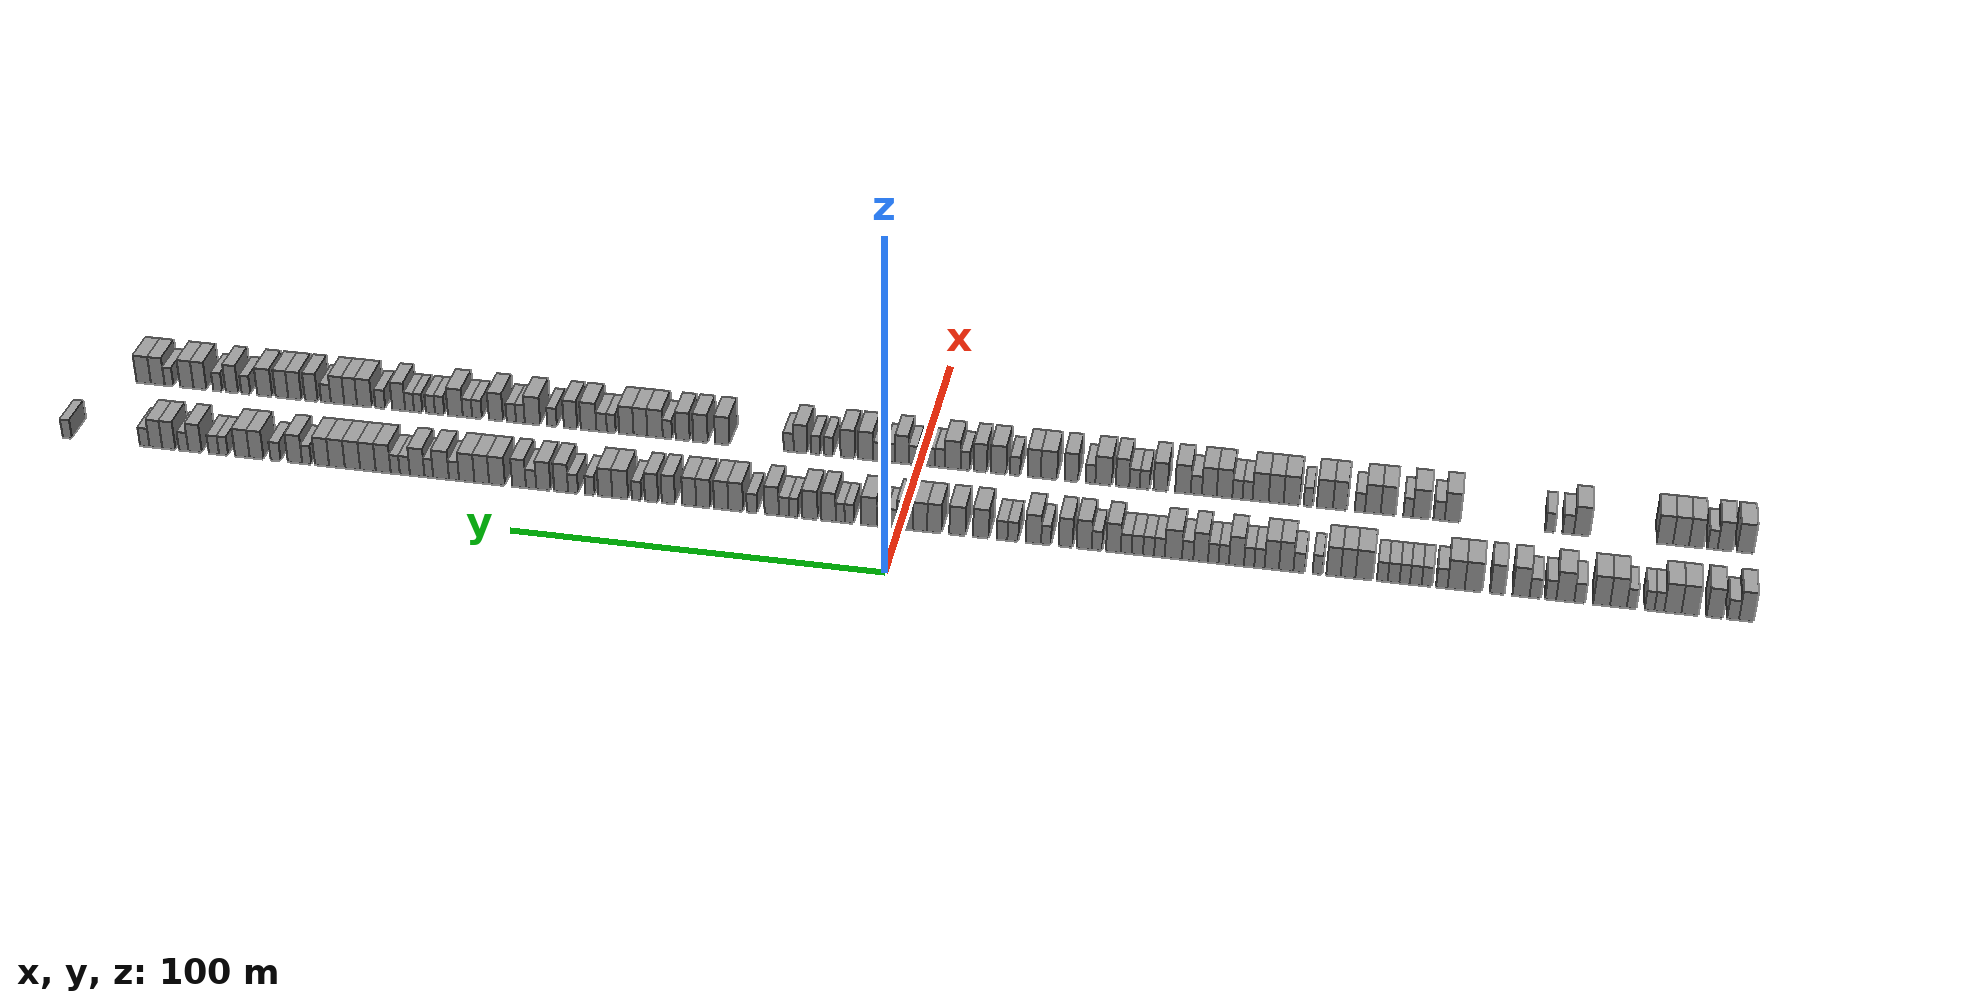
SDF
<sdf version="1.6">
 <world name="default">
  <scene>
   <sky><clouds><speed>12</speed></clouds></sky>
   <ambient>0.4 0.4 0.4 1</ambient>
   <background>0.7 0.7 0.7 1</background>
   <shadows>1</shadows>
  </scene>
  <gravity>0 0 -9.8066</gravity>
  <magnetic_field>6e-06 2.3e-05 -4.2e-05</magnetic_field>
  <physics default="0" name="default_physics" type="ode">
   <ode>
    <solver>
     <type>quick</type>
     <iters>10</iters>
     <sor>1.0</sor>
     <use_dynamic_moi_rescaling>0</use_dynamic_moi_rescaling>
    </solver>
    <constraints>
     <cfm>0</cfm>
     <erp>0.2</erp>
     <contact_max_correcting_vel>100</contact_max_correcting_vel>
     <contact_surface_layer>0.001</contact_surface_layer>
    </constraints>
   </ode>
   <max_step_size>0.004</max_step_size>
   <real_time_factor>1</real_time_factor>
   <real_time_update_rate>250</real_time_update_rate>
  </physics>
  <light name="sun" type="directional">
   <pose>0 0 10 0 0 0</pose>
   <diffuse>0.8 0.8 0.8 1</diffuse>
   <specular>0.2 0.2 0.2 1</specular>
   <attenuation>
    <range>1000</range>
    <constant>0.9</constant>
    <linear>0.01</linear>
    <quadratic>0.001</quadratic>
   </attenuation>
   <direction>-0.5 0.1 -0.9</direction>
  </light>
  <model name="building_1">
   <static>1</static>
   <pose>25.0000 -217.1671 0 0.000000 0.000000 0.000000</pose>
   <link name="link">
    <pose>0 0 4.50 0 0 0</pose>
    <collision name="collision"><geometry><box><size>10.0000 3.6659 9.0000</size></box></geometry></collision>
    <visual name="visual">
     <cast_shadows>0</cast_shadows>
     <geometry><box><size>10.0000 3.6659 9.0000</size></box></geometry>
     <material>
      <script>
       <uri>model://grey_wall/materials/scripts</uri>
       <uri>model://grey_wall/materials/textures</uri>
       <name>vrc/grey_wall</name>
      </script>
     </material>
    </visual>
   </link>
  </model>
  <model name="building_2">
   <static>1</static>
   <pose>25.0000 -213.8735 0 0.000000 0.000000 0.000000</pose>
   <link name="link">
    <pose>0 0 3.00 0 0 0</pose>
    <collision name="collision"><geometry><box><size>10.0000 2.9212 6.0000</size></box></geometry></collision>
    <visual name="visual">
     <cast_shadows>0</cast_shadows>
     <geometry><box><size>10.0000 2.9212 6.0000</size></box></geometry>
     <material>
      <script>
       <uri>model://grey_wall/materials/scripts</uri>
       <uri>model://grey_wall/materials/textures</uri>
       <name>vrc/grey_wall</name>
      </script>
     </material>
    </visual>
   </link>
  </model>
  <model name="building_3">
   <static>1</static>
   <pose>25.0000 -209.3716 0 0.000000 0.000000 0.000000</pose>
   <link name="link">
    <pose>0 0 4.50 0 0 0</pose>
    <collision name="collision"><geometry><box><size>10.0000 4.0827 9.0000</size></box></geometry></collision>
    <visual name="visual">
     <cast_shadows>0</cast_shadows>
     <geometry><box><size>10.0000 4.0827 9.0000</size></box></geometry>
     <material>
      <script>
       <uri>model://grey_wall/materials/scripts</uri>
       <uri>model://grey_wall/materials/textures</uri>
       <name>vrc/grey_wall</name>
      </script>
     </material>
    </visual>
   </link>
  </model>
  <model name="building_4">
   <static>1</static>
   <pose>25.0000 -203.2001 0 0.000000 0.000000 0.000000</pose>
   <link name="link">
    <pose>0 0 4.50 0 0 0</pose>
    <collision name="collision"><geometry><box><size>10.0000 4.2603 9.0000</size></box></geometry></collision>
    <visual name="visual">
     <cast_shadows>0</cast_shadows>
     <geometry><box><size>10.0000 4.2603 9.0000</size></box></geometry>
     <material>
      <script>
       <uri>model://grey_wall/materials/scripts</uri>
       <uri>model://grey_wall/materials/textures</uri>
       <name>vrc/grey_wall</name>
      </script>
     </material>
    </visual>
   </link>
  </model>
  <model name="building_5">
   <static>1</static>
   <pose>25.0000 -198.9381 0 0.000000 0.000000 0.000000</pose>
   <link name="link">
    <pose>0 0 4.50 0 0 0</pose>
    <collision name="collision"><geometry><box><size>10.0000 4.2636 9.0000</size></box></geometry></collision>
    <visual name="visual">
     <cast_shadows>0</cast_shadows>
     <geometry><box><size>10.0000 4.2636 9.0000</size></box></geometry>
     <material>
      <script>
       <uri>model://grey_wall/materials/scripts</uri>
       <uri>model://grey_wall/materials/textures</uri>
       <name>vrc/grey_wall</name>
      </script>
     </material>
    </visual>
   </link>
  </model>
  <model name="building_6">
   <static>1</static>
   <pose>25.0000 -195.5967 0 0.000000 0.000000 0.000000</pose>
   <link name="link">
    <pose>0 0 3.00 0 0 0</pose>
    <collision name="collision"><geometry><box><size>10.0000 2.4193 6.0000</size></box></geometry></collision>
    <visual name="visual">
     <cast_shadows>0</cast_shadows>
     <geometry><box><size>10.0000 2.4193 6.0000</size></box></geometry>
     <material>
      <script>
       <uri>model://grey_wall/materials/scripts</uri>
       <uri>model://grey_wall/materials/textures</uri>
       <name>vrc/grey_wall</name>
      </script>
     </material>
    </visual>
   </link>
  </model>
  <model name="building_7">
   <static>1</static>
   <pose>25.0000 -193.1771 0 0.000000 0.000000 0.000000</pose>
   <link name="link">
    <pose>0 0 3.00 0 0 0</pose>
    <collision name="collision"><geometry><box><size>10.0000 2.4199 6.0000</size></box></geometry></collision>
    <visual name="visual">
     <cast_shadows>0</cast_shadows>
     <geometry><box><size>10.0000 2.4199 6.0000</size></box></geometry>
     <material>
      <script>
       <uri>model://grey_wall/materials/scripts</uri>
       <uri>model://grey_wall/materials/textures</uri>
       <name>vrc/grey_wall</name>
      </script>
     </material>
    </visual>
   </link>
  </model>
  <model name="building_8">
   <static>1</static>
   <pose>25.0000 -188.7444 0 0.000000 0.000000 0.000000</pose>
   <link name="link">
    <pose>0 0 3.00 0 0 0</pose>
    <collision name="collision"><geometry><box><size>10.0000 2.4454 6.0000</size></box></geometry></collision>
    <visual name="visual">
     <cast_shadows>0</cast_shadows>
     <geometry><box><size>10.0000 2.4454 6.0000</size></box></geometry>
     <material>
      <script>
       <uri>model://grey_wall/materials/scripts</uri>
       <uri>model://grey_wall/materials/textures</uri>
       <name>vrc/grey_wall</name>
      </script>
     </material>
    </visual>
   </link>
  </model>
  <model name="building_9">
   <static>1</static>
   <pose>25.0000 -185.4251 0 0.000000 0.000000 0.000000</pose>
   <link name="link">
    <pose>0 0 4.50 0 0 0</pose>
    <collision name="collision"><geometry><box><size>10.0000 4.1932 9.0000</size></box></geometry></collision>
    <visual name="visual">
     <cast_shadows>0</cast_shadows>
     <geometry><box><size>10.0000 4.1932 9.0000</size></box></geometry>
     <material>
      <script>
       <uri>model://grey_wall/materials/scripts</uri>
       <uri>model://grey_wall/materials/textures</uri>
       <name>vrc/grey_wall</name>
      </script>
     </material>
    </visual>
   </link>
  </model>
  <model name="building_10">
   <static>1</static>
   <pose>25.0000 -181.2285 0 0.000000 0.000000 0.000000</pose>
   <link name="link">
    <pose>0 0 4.50 0 0 0</pose>
    <collision name="collision"><geometry><box><size>10.0000 4.2000 9.0000</size></box></geometry></collision>
    <visual name="visual">
     <cast_shadows>0</cast_shadows>
     <geometry><box><size>10.0000 4.2000 9.0000</size></box></geometry>
     <material>
      <script>
       <uri>model://grey_wall/materials/scripts</uri>
       <uri>model://grey_wall/materials/textures</uri>
       <name>vrc/grey_wall</name>
      </script>
     </material>
    </visual>
   </link>
  </model>
  <model name="building_11">
   <static>1</static>
   <pose>25.0000 -175.7591 0 0.000000 0.000000 0.000000</pose>
   <link name="link">
    <pose>0 0 3.00 0 0 0</pose>
    <collision name="collision"><geometry><box><size>10.0000 2.7388 6.0000</size></box></geometry></collision>
    <visual name="visual">
     <cast_shadows>0</cast_shadows>
     <geometry><box><size>10.0000 2.7388 6.0000</size></box></geometry>
     <material>
      <script>
       <uri>model://grey_wall/materials/scripts</uri>
       <uri>model://grey_wall/materials/textures</uri>
       <name>vrc/grey_wall</name>
      </script>
     </material>
    </visual>
   </link>
  </model>
  <model name="building_12">
   <static>1</static>
   <pose>25.0000 -172.1402 0 0.000000 0.000000 0.000000</pose>
   <link name="link">
    <pose>0 0 4.50 0 0 0</pose>
    <collision name="collision"><geometry><box><size>10.0000 4.4991 9.0000</size></box></geometry></collision>
    <visual name="visual">
     <cast_shadows>0</cast_shadows>
     <geometry><box><size>10.0000 4.4991 9.0000</size></box></geometry>
     <material>
      <script>
       <uri>model://grey_wall/materials/scripts</uri>
       <uri>model://grey_wall/materials/textures</uri>
       <name>vrc/grey_wall</name>
      </script>
     </material>
    </visual>
   </link>
  </model>
  <model name="building_13">
   <static>1</static>
   <pose>25.0000 -168.5023 0 0.000000 0.000000 0.000000</pose>
   <link name="link">
    <pose>0 0 3.00 0 0 0</pose>
    <collision name="collision"><geometry><box><size>10.0000 2.7767 6.0000</size></box></geometry></collision>
    <visual name="visual">
     <cast_shadows>0</cast_shadows>
     <geometry><box><size>10.0000 2.7767 6.0000</size></box></geometry>
     <material>
      <script>
       <uri>model://grey_wall/materials/scripts</uri>
       <uri>model://grey_wall/materials/textures</uri>
       <name>vrc/grey_wall</name>
      </script>
     </material>
    </visual>
   </link>
  </model>
  <model name="building_14">
   <static>1</static>
   <pose>25.0000 -164.6484 0 0.000000 0.000000 0.000000</pose>
   <link name="link">
    <pose>0 0 3.00 0 0 0</pose>
    <collision name="collision"><geometry><box><size>10.0000 2.9310 6.0000</size></box></geometry></collision>
    <visual name="visual">
     <cast_shadows>0</cast_shadows>
     <geometry><box><size>10.0000 2.9310 6.0000</size></box></geometry>
     <material>
      <script>
       <uri>model://grey_wall/materials/scripts</uri>
       <uri>model://grey_wall/materials/textures</uri>
       <name>vrc/grey_wall</name>
      </script>
     </material>
    </visual>
   </link>
  </model>
  <model name="building_15">
   <static>1</static>
   <pose>25.0000 -161.0380 0 0.000000 0.000000 0.000000</pose>
   <link name="link">
    <pose>0 0 4.50 0 0 0</pose>
    <collision name="collision"><geometry><box><size>10.0000 4.2898 9.0000</size></box></geometry></collision>
    <visual name="visual">
     <cast_shadows>0</cast_shadows>
     <geometry><box><size>10.0000 4.2898 9.0000</size></box></geometry>
     <material>
      <script>
       <uri>model://grey_wall/materials/scripts</uri>
       <uri>model://grey_wall/materials/textures</uri>
       <name>vrc/grey_wall</name>
      </script>
     </material>
    </visual>
   </link>
  </model>
  <model name="building_16">
   <static>1</static>
   <pose>25.0000 -155.0702 0 0.000000 0.000000 0.000000</pose>
   <link name="link">
    <pose>0 0 4.50 0 0 0</pose>
    <collision name="collision"><geometry><box><size>10.0000 3.6458 9.0000</size></box></geometry></collision>
    <visual name="visual">
     <cast_shadows>0</cast_shadows>
     <geometry><box><size>10.0000 3.6458 9.0000</size></box></geometry>
     <material>
      <script>
       <uri>model://grey_wall/materials/scripts</uri>
       <uri>model://grey_wall/materials/textures</uri>
       <name>vrc/grey_wall</name>
      </script>
     </material>
    </visual>
   </link>
  </model>
  <model name="building_17">
   <static>1</static>
   <pose>25.0000 -149.0126 0 0.000000 0.000000 0.000000</pose>
   <link name="link">
    <pose>0 0 4.50 0 0 0</pose>
    <collision name="collision"><geometry><box><size>10.0000 4.4693 9.0000</size></box></geometry></collision>
    <visual name="visual">
     <cast_shadows>0</cast_shadows>
     <geometry><box><size>10.0000 4.4693 9.0000</size></box></geometry>
     <material>
      <script>
       <uri>model://grey_wall/materials/scripts</uri>
       <uri>model://grey_wall/materials/textures</uri>
       <name>vrc/grey_wall</name>
      </script>
     </material>
    </visual>
   </link>
  </model>
  <model name="building_18">
   <static>1</static>
   <pose>25.0000 -144.6236 0 0.000000 0.000000 0.000000</pose>
   <link name="link">
    <pose>0 0 4.50 0 0 0</pose>
    <collision name="collision"><geometry><box><size>10.0000 4.3088 9.0000</size></box></geometry></collision>
    <visual name="visual">
     <cast_shadows>0</cast_shadows>
     <geometry><box><size>10.0000 4.3088 9.0000</size></box></geometry>
     <material>
      <script>
       <uri>model://grey_wall/materials/scripts</uri>
       <uri>model://grey_wall/materials/textures</uri>
       <name>vrc/grey_wall</name>
      </script>
     </material>
    </visual>
   </link>
  </model>
  <model name="building_19">
   <static>1</static>
   <pose>25.0000 -141.0324 0 0.000000 0.000000 0.000000</pose>
   <link name="link">
    <pose>0 0 3.00 0 0 0</pose>
    <collision name="collision"><geometry><box><size>10.0000 2.8735 6.0000</size></box></geometry></collision>
    <visual name="visual">
     <cast_shadows>0</cast_shadows>
     <geometry><box><size>10.0000 2.8735 6.0000</size></box></geometry>
     <material>
      <script>
       <uri>model://grey_wall/materials/scripts</uri>
       <uri>model://grey_wall/materials/textures</uri>
       <name>vrc/grey_wall</name>
      </script>
     </material>
    </visual>
   </link>
  </model>
  <model name="building_20">
   <static>1</static>
   <pose>25.0000 -137.2617 0 0.000000 0.000000 0.000000</pose>
   <link name="link">
    <pose>0 0 3.00 0 0 0</pose>
    <collision name="collision"><geometry><box><size>10.0000 2.6680 6.0000</size></box></geometry></collision>
    <visual name="visual">
     <cast_shadows>0</cast_shadows>
     <geometry><box><size>10.0000 2.6680 6.0000</size></box></geometry>
     <material>
      <script>
       <uri>model://grey_wall/materials/scripts</uri>
       <uri>model://grey_wall/materials/textures</uri>
       <name>vrc/grey_wall</name>
      </script>
     </material>
    </visual>
   </link>
  </model>
  <model name="building_21">
   <static>1</static>
   <pose>25.0000 -134.4380 0 0.000000 0.000000 0.000000</pose>
   <link name="link">
    <pose>0 0 3.00 0 0 0</pose>
    <collision name="collision"><geometry><box><size>10.0000 2.9795 6.0000</size></box></geometry></collision>
    <visual name="visual">
     <cast_shadows>0</cast_shadows>
     <geometry><box><size>10.0000 2.9795 6.0000</size></box></geometry>
     <material>
      <script>
       <uri>model://grey_wall/materials/scripts</uri>
       <uri>model://grey_wall/materials/textures</uri>
       <name>vrc/grey_wall</name>
      </script>
     </material>
    </visual>
   </link>
  </model>
  <model name="building_22">
   <static>1</static>
   <pose>25.0000 -131.6081 0 0.000000 0.000000 0.000000</pose>
   <link name="link">
    <pose>0 0 3.00 0 0 0</pose>
    <collision name="collision"><geometry><box><size>10.0000 2.6803 6.0000</size></box></geometry></collision>
    <visual name="visual">
     <cast_shadows>0</cast_shadows>
     <geometry><box><size>10.0000 2.6803 6.0000</size></box></geometry>
     <material>
      <script>
       <uri>model://grey_wall/materials/scripts</uri>
       <uri>model://grey_wall/materials/textures</uri>
       <name>vrc/grey_wall</name>
      </script>
     </material>
    </visual>
   </link>
  </model>
  <model name="building_23">
   <static>1</static>
   <pose>25.0000 -128.7739 0 0.000000 0.000000 0.000000</pose>
   <link name="link">
    <pose>0 0 3.00 0 0 0</pose>
    <collision name="collision"><geometry><box><size>10.0000 2.9879 6.0000</size></box></geometry></collision>
    <visual name="visual">
     <cast_shadows>0</cast_shadows>
     <geometry><box><size>10.0000 2.9879 6.0000</size></box></geometry>
     <material>
      <script>
       <uri>model://grey_wall/materials/scripts</uri>
       <uri>model://grey_wall/materials/textures</uri>
       <name>vrc/grey_wall</name>
      </script>
     </material>
    </visual>
   </link>
  </model>
  <model name="building_24">
   <static>1</static>
   <pose>25.0000 -125.8931 0 0.000000 0.000000 0.000000</pose>
   <link name="link">
    <pose>0 0 3.00 0 0 0</pose>
    <collision name="collision"><geometry><box><size>10.0000 2.7739 6.0000</size></box></geometry></collision>
    <visual name="visual">
     <cast_shadows>0</cast_shadows>
     <geometry><box><size>10.0000 2.7739 6.0000</size></box></geometry>
     <material>
      <script>
       <uri>model://grey_wall/materials/scripts</uri>
       <uri>model://grey_wall/materials/textures</uri>
       <name>vrc/grey_wall</name>
      </script>
     </material>
    </visual>
   </link>
  </model>
  <model name="building_25">
   <static>1</static>
   <pose>25.0000 -121.2723 0 0.000000 0.000000 0.000000</pose>
   <link name="link">
    <pose>0 0 4.50 0 0 0</pose>
    <collision name="collision"><geometry><box><size>10.0000 4.4677 9.0000</size></box></geometry></collision>
    <visual name="visual">
     <cast_shadows>0</cast_shadows>
     <geometry><box><size>10.0000 4.4677 9.0000</size></box></geometry>
     <material>
      <script>
       <uri>model://grey_wall/materials/scripts</uri>
       <uri>model://grey_wall/materials/textures</uri>
       <name>vrc/grey_wall</name>
      </script>
     </material>
    </visual>
   </link>
  </model>
  <model name="building_26">
   <static>1</static>
   <pose>25.0000 -117.1486 0 0.000000 0.000000 0.000000</pose>
   <link name="link">
    <pose>0 0 4.50 0 0 0</pose>
    <collision name="collision"><geometry><box><size>10.0000 3.7798 9.0000</size></box></geometry></collision>
    <visual name="visual">
     <cast_shadows>0</cast_shadows>
     <geometry><box><size>10.0000 3.7798 9.0000</size></box></geometry>
     <material>
      <script>
       <uri>model://grey_wall/materials/scripts</uri>
       <uri>model://grey_wall/materials/textures</uri>
       <name>vrc/grey_wall</name>
      </script>
     </material>
    </visual>
   </link>
  </model>
  <model name="building_27">
   <static>1</static>
   <pose>25.0000 -113.4258 0 0.000000 0.000000 0.000000</pose>
   <link name="link">
    <pose>0 0 4.50 0 0 0</pose>
    <collision name="collision"><geometry><box><size>10.0000 3.6658 9.0000</size></box></geometry></collision>
    <visual name="visual">
     <cast_shadows>0</cast_shadows>
     <geometry><box><size>10.0000 3.6658 9.0000</size></box></geometry>
     <material>
      <script>
       <uri>model://grey_wall/materials/scripts</uri>
       <uri>model://grey_wall/materials/textures</uri>
       <name>vrc/grey_wall</name>
      </script>
     </material>
    </visual>
   </link>
  </model>
  <model name="building_28">
   <static>1</static>
   <pose>25.0000 -109.3301 0 0.000000 0.000000 0.000000</pose>
   <link name="link">
    <pose>0 0 3.00 0 0 0</pose>
    <collision name="collision"><geometry><box><size>10.0000 2.5256 6.0000</size></box></geometry></collision>
    <visual name="visual">
     <cast_shadows>0</cast_shadows>
     <geometry><box><size>10.0000 2.5256 6.0000</size></box></geometry>
     <material>
      <script>
       <uri>model://grey_wall/materials/scripts</uri>
       <uri>model://grey_wall/materials/textures</uri>
       <name>vrc/grey_wall</name>
      </script>
     </material>
    </visual>
   </link>
  </model>
  <model name="building_29">
   <static>1</static>
   <pose>25.0000 -104.5966 0 0.000000 0.000000 0.000000</pose>
   <link name="link">
    <pose>0 0 3.00 0 0 0</pose>
    <collision name="collision"><geometry><box><size>10.0000 2.9414 6.0000</size></box></geometry></collision>
    <visual name="visual">
     <cast_shadows>0</cast_shadows>
     <geometry><box><size>10.0000 2.9414 6.0000</size></box></geometry>
     <material>
      <script>
       <uri>model://grey_wall/materials/scripts</uri>
       <uri>model://grey_wall/materials/textures</uri>
       <name>vrc/grey_wall</name>
      </script>
     </material>
    </visual>
   </link>
  </model>
  <model name="building_30">
   <static>1</static>
   <pose>25.0000 -101.2687 0 0.000000 0.000000 0.000000</pose>
   <link name="link">
    <pose>0 0 4.50 0 0 0</pose>
    <collision name="collision"><geometry><box><size>10.0000 3.7144 9.0000</size></box></geometry></collision>
    <visual name="visual">
     <cast_shadows>0</cast_shadows>
     <geometry><box><size>10.0000 3.7144 9.0000</size></box></geometry>
     <material>
      <script>
       <uri>model://grey_wall/materials/scripts</uri>
       <uri>model://grey_wall/materials/textures</uri>
       <name>vrc/grey_wall</name>
      </script>
     </material>
    </visual>
   </link>
  </model>
  <model name="building_31">
   <static>1</static>
   <pose>25.0000 -97.5562 0 0.000000 0.000000 0.000000</pose>
   <link name="link">
    <pose>0 0 4.50 0 0 0</pose>
    <collision name="collision"><geometry><box><size>10.0000 3.7105 9.0000</size></box></geometry></collision>
    <visual name="visual">
     <cast_shadows>0</cast_shadows>
     <geometry><box><size>10.0000 3.7105 9.0000</size></box></geometry>
     <material>
      <script>
       <uri>model://grey_wall/materials/scripts</uri>
       <uri>model://grey_wall/materials/textures</uri>
       <name>vrc/grey_wall</name>
      </script>
     </material>
    </visual>
   </link>
  </model>
  <model name="building_32">
   <static>1</static>
   <pose>25.0000 -94.3791 0 0.000000 0.000000 0.000000</pose>
   <link name="link">
    <pose>0 0 3.00 0 0 0</pose>
    <collision name="collision"><geometry><box><size>10.0000 2.6438 6.0000</size></box></geometry></collision>
    <visual name="visual">
     <cast_shadows>0</cast_shadows>
     <geometry><box><size>10.0000 2.6438 6.0000</size></box></geometry>
     <material>
      <script>
       <uri>model://grey_wall/materials/scripts</uri>
       <uri>model://grey_wall/materials/textures</uri>
       <name>vrc/grey_wall</name>
      </script>
     </material>
    </visual>
   </link>
  </model>
  <model name="building_33">
   <static>1</static>
   <pose>25.0000 -91.7267 0 0.000000 0.000000 0.000000</pose>
   <link name="link">
    <pose>0 0 3.00 0 0 0</pose>
    <collision name="collision"><geometry><box><size>10.0000 2.6610 6.0000</size></box></geometry></collision>
    <visual name="visual">
     <cast_shadows>0</cast_shadows>
     <geometry><box><size>10.0000 2.6610 6.0000</size></box></geometry>
     <material>
      <script>
       <uri>model://grey_wall/materials/scripts</uri>
       <uri>model://grey_wall/materials/textures</uri>
       <name>vrc/grey_wall</name>
      </script>
     </material>
    </visual>
   </link>
  </model>
  <model name="building_34">
   <static>1</static>
   <pose>25.0000 -88.4462 0 0.000000 0.000000 0.000000</pose>
   <link name="link">
    <pose>0 0 4.50 0 0 0</pose>
    <collision name="collision"><geometry><box><size>10.0000 3.9000 9.0000</size></box></geometry></collision>
    <visual name="visual">
     <cast_shadows>0</cast_shadows>
     <geometry><box><size>10.0000 3.9000 9.0000</size></box></geometry>
     <material>
      <script>
       <uri>model://grey_wall/materials/scripts</uri>
       <uri>model://grey_wall/materials/textures</uri>
       <name>vrc/grey_wall</name>
      </script>
     </material>
    </visual>
   </link>
  </model>
  <model name="building_35">
   <static>1</static>
   <pose>25.0000 -85.1547 0 0.000000 0.000000 0.000000</pose>
   <link name="link">
    <pose>0 0 3.00 0 0 0</pose>
    <collision name="collision"><geometry><box><size>10.0000 2.6829 6.0000</size></box></geometry></collision>
    <visual name="visual">
     <cast_shadows>0</cast_shadows>
     <geometry><box><size>10.0000 2.6829 6.0000</size></box></geometry>
     <material>
      <script>
       <uri>model://grey_wall/materials/scripts</uri>
       <uri>model://grey_wall/materials/textures</uri>
       <name>vrc/grey_wall</name>
      </script>
     </material>
    </visual>
   </link>
  </model>
  <model name="building_36">
   <static>1</static>
   <pose>25.0000 -82.4580 0 0.000000 0.000000 0.000000</pose>
   <link name="link">
    <pose>0 0 3.00 0 0 0</pose>
    <collision name="collision"><geometry><box><size>10.0000 2.7106 6.0000</size></box></geometry></collision>
    <visual name="visual">
     <cast_shadows>0</cast_shadows>
     <geometry><box><size>10.0000 2.7106 6.0000</size></box></geometry>
     <material>
      <script>
       <uri>model://grey_wall/materials/scripts</uri>
       <uri>model://grey_wall/materials/textures</uri>
       <name>vrc/grey_wall</name>
      </script>
     </material>
    </visual>
   </link>
  </model>
  <model name="building_37">
   <static>1</static>
   <pose>25.0000 -79.1855 0 0.000000 0.000000 0.000000</pose>
   <link name="link">
    <pose>0 0 4.50 0 0 0</pose>
    <collision name="collision"><geometry><box><size>10.0000 3.8344 9.0000</size></box></geometry></collision>
    <visual name="visual">
     <cast_shadows>0</cast_shadows>
     <geometry><box><size>10.0000 3.8344 9.0000</size></box></geometry>
     <material>
      <script>
       <uri>model://grey_wall/materials/scripts</uri>
       <uri>model://grey_wall/materials/textures</uri>
       <name>vrc/grey_wall</name>
      </script>
     </material>
    </visual>
   </link>
  </model>
  <model name="building_38">
   <static>1</static>
   <pose>25.0000 -75.8074 0 0.000000 0.000000 0.000000</pose>
   <link name="link">
    <pose>0 0 3.00 0 0 0</pose>
    <collision name="collision"><geometry><box><size>10.0000 2.9218 6.0000</size></box></geometry></collision>
    <visual name="visual">
     <cast_shadows>0</cast_shadows>
     <geometry><box><size>10.0000 2.9218 6.0000</size></box></geometry>
     <material>
      <script>
       <uri>model://grey_wall/materials/scripts</uri>
       <uri>model://grey_wall/materials/textures</uri>
       <name>vrc/grey_wall</name>
      </script>
     </material>
    </visual>
   </link>
  </model>
  <model name="building_39">
   <static>1</static>
   <pose>25.0000 -72.1008 0 0.000000 0.000000 0.000000</pose>
   <link name="link">
    <pose>0 0 4.50 0 0 0</pose>
    <collision name="collision"><geometry><box><size>10.0000 4.4913 9.0000</size></box></geometry></collision>
    <visual name="visual">
     <cast_shadows>0</cast_shadows>
     <geometry><box><size>10.0000 4.4913 9.0000</size></box></geometry>
     <material>
      <script>
       <uri>model://grey_wall/materials/scripts</uri>
       <uri>model://grey_wall/materials/textures</uri>
       <name>vrc/grey_wall</name>
      </script>
     </material>
    </visual>
   </link>
  </model>
  <model name="building_40">
   <static>1</static>
   <pose>25.0000 -68.4680 0 0.000000 0.000000 0.000000</pose>
   <link name="link">
    <pose>0 0 3.00 0 0 0</pose>
    <collision name="collision"><geometry><box><size>10.0000 2.7743 6.0000</size></box></geometry></collision>
    <visual name="visual">
     <cast_shadows>0</cast_shadows>
     <geometry><box><size>10.0000 2.7743 6.0000</size></box></geometry>
     <material>
      <script>
       <uri>model://grey_wall/materials/scripts</uri>
       <uri>model://grey_wall/materials/textures</uri>
       <name>vrc/grey_wall</name>
      </script>
     </material>
    </visual>
   </link>
  </model>
  <model name="building_41">
   <static>1</static>
   <pose>25.0000 -65.6387 0 0.000000 0.000000 0.000000</pose>
   <link name="link">
    <pose>0 0 3.00 0 0 0</pose>
    <collision name="collision"><geometry><box><size>10.0000 2.8842 6.0000</size></box></geometry></collision>
    <visual name="visual">
     <cast_shadows>0</cast_shadows>
     <geometry><box><size>10.0000 2.8842 6.0000</size></box></geometry>
     <material>
      <script>
       <uri>model://grey_wall/materials/scripts</uri>
       <uri>model://grey_wall/materials/textures</uri>
       <name>vrc/grey_wall</name>
      </script>
     </material>
    </visual>
   </link>
  </model>
  <model name="building_42">
   <static>1</static>
   <pose>25.0000 -62.7112 0 0.000000 0.000000 0.000000</pose>
   <link name="link">
    <pose>0 0 3.00 0 0 0</pose>
    <collision name="collision"><geometry><box><size>10.0000 2.9709 6.0000</size></box></geometry></collision>
    <visual name="visual">
     <cast_shadows>0</cast_shadows>
     <geometry><box><size>10.0000 2.9709 6.0000</size></box></geometry>
     <material>
      <script>
       <uri>model://grey_wall/materials/scripts</uri>
       <uri>model://grey_wall/materials/textures</uri>
       <name>vrc/grey_wall</name>
      </script>
     </material>
    </visual>
   </link>
  </model>
  <model name="building_43">
   <static>1</static>
   <pose>25.0000 -59.8007 0 0.000000 0.000000 0.000000</pose>
   <link name="link">
    <pose>0 0 3.00 0 0 0</pose>
    <collision name="collision"><geometry><box><size>10.0000 2.8501 6.0000</size></box></geometry></collision>
    <visual name="visual">
     <cast_shadows>0</cast_shadows>
     <geometry><box><size>10.0000 2.8501 6.0000</size></box></geometry>
     <material>
      <script>
       <uri>model://grey_wall/materials/scripts</uri>
       <uri>model://grey_wall/materials/textures</uri>
       <name>vrc/grey_wall</name>
      </script>
     </material>
    </visual>
   </link>
  </model>
  <model name="building_44">
   <static>1</static>
   <pose>25.0000 -56.4494 0 0.000000 0.000000 0.000000</pose>
   <link name="link">
    <pose>0 0 4.50 0 0 0</pose>
    <collision name="collision"><geometry><box><size>10.0000 3.8525 9.0000</size></box></geometry></collision>
    <visual name="visual">
     <cast_shadows>0</cast_shadows>
     <geometry><box><size>10.0000 3.8525 9.0000</size></box></geometry>
     <material>
      <script>
       <uri>model://grey_wall/materials/scripts</uri>
       <uri>model://grey_wall/materials/textures</uri>
       <name>vrc/grey_wall</name>
      </script>
     </material>
    </visual>
   </link>
  </model>
  <model name="building_45">
   <static>1</static>
   <pose>25.0000 -52.1602 0 0.000000 0.000000 0.000000</pose>
   <link name="link">
    <pose>0 0 3.00 0 0 0</pose>
    <collision name="collision"><geometry><box><size>10.0000 2.7258 6.0000</size></box></geometry></collision>
    <visual name="visual">
     <cast_shadows>0</cast_shadows>
     <geometry><box><size>10.0000 2.7258 6.0000</size></box></geometry>
     <material>
      <script>
       <uri>model://grey_wall/materials/scripts</uri>
       <uri>model://grey_wall/materials/textures</uri>
       <name>vrc/grey_wall</name>
      </script>
     </material>
    </visual>
   </link>
  </model>
  <model name="building_46">
   <static>1</static>
   <pose>25.0000 -48.8019 0 0.000000 0.000000 0.000000</pose>
   <link name="link">
    <pose>0 0 4.50 0 0 0</pose>
    <collision name="collision"><geometry><box><size>10.0000 3.9910 9.0000</size></box></geometry></collision>
    <visual name="visual">
     <cast_shadows>0</cast_shadows>
     <geometry><box><size>10.0000 3.9910 9.0000</size></box></geometry>
     <material>
      <script>
       <uri>model://grey_wall/materials/scripts</uri>
       <uri>model://grey_wall/materials/textures</uri>
       <name>vrc/grey_wall</name>
      </script>
     </material>
    </visual>
   </link>
  </model>
  <model name="building_47">
   <static>1</static>
   <pose>25.0000 -43.9524 0 0.000000 0.000000 0.000000</pose>
   <link name="link">
    <pose>0 0 4.50 0 0 0</pose>
    <collision name="collision"><geometry><box><size>10.0000 3.7080 9.0000</size></box></geometry></collision>
    <visual name="visual">
     <cast_shadows>0</cast_shadows>
     <geometry><box><size>10.0000 3.7080 9.0000</size></box></geometry>
     <material>
      <script>
       <uri>model://grey_wall/materials/scripts</uri>
       <uri>model://grey_wall/materials/textures</uri>
       <name>vrc/grey_wall</name>
      </script>
     </material>
    </visual>
   </link>
  </model>
  <model name="building_48">
   <static>1</static>
   <pose>25.0000 -38.8013 0 0.000000 0.000000 0.000000</pose>
   <link name="link">
    <pose>0 0 3.00 0 0 0</pose>
    <collision name="collision"><geometry><box><size>10.0000 2.5941 6.0000</size></box></geometry></collision>
    <visual name="visual">
     <cast_shadows>0</cast_shadows>
     <geometry><box><size>10.0000 2.5941 6.0000</size></box></geometry>
     <material>
      <script>
       <uri>model://grey_wall/materials/scripts</uri>
       <uri>model://grey_wall/materials/textures</uri>
       <name>vrc/grey_wall</name>
      </script>
     </material>
    </visual>
   </link>
  </model>
  <model name="building_49">
   <static>1</static>
   <pose>25.0000 -35.4844 0 0.000000 0.000000 0.000000</pose>
   <link name="link">
    <pose>0 0 4.50 0 0 0</pose>
    <collision name="collision"><geometry><box><size>10.0000 4.0397 9.0000</size></box></geometry></collision>
    <visual name="visual">
     <cast_shadows>0</cast_shadows>
     <geometry><box><size>10.0000 4.0397 9.0000</size></box></geometry>
     <material>
      <script>
       <uri>model://grey_wall/materials/scripts</uri>
       <uri>model://grey_wall/materials/textures</uri>
       <name>vrc/grey_wall</name>
      </script>
     </material>
    </visual>
   </link>
  </model>
  <model name="building_50">
   <static>1</static>
   <pose>25.0000 -30.0270 0 0.000000 0.000000 0.000000</pose>
   <link name="link">
    <pose>0 0 3.00 0 0 0</pose>
    <collision name="collision"><geometry><box><size>10.0000 2.8750 6.0000</size></box></geometry></collision>
    <visual name="visual">
     <cast_shadows>0</cast_shadows>
     <geometry><box><size>10.0000 2.8750 6.0000</size></box></geometry>
     <material>
      <script>
       <uri>model://grey_wall/materials/scripts</uri>
       <uri>model://grey_wall/materials/textures</uri>
       <name>vrc/grey_wall</name>
      </script>
     </material>
    </visual>
   </link>
  </model>
  <model name="building_51">
   <static>1</static>
   <pose>25.0000 -27.1659 0 0.000000 0.000000 0.000000</pose>
   <link name="link">
    <pose>0 0 3.00 0 0 0</pose>
    <collision name="collision"><geometry><box><size>10.0000 2.8471 6.0000</size></box></geometry></collision>
    <visual name="visual">
     <cast_shadows>0</cast_shadows>
     <geometry><box><size>10.0000 2.8471 6.0000</size></box></geometry>
     <material>
      <script>
       <uri>model://grey_wall/materials/scripts</uri>
       <uri>model://grey_wall/materials/textures</uri>
       <name>vrc/grey_wall</name>
      </script>
     </material>
    </visual>
   </link>
  </model>
  <model name="building_52">
   <static>1</static>
   <pose>25.0000 -21.6329 0 0.000000 0.000000 0.000000</pose>
   <link name="link">
    <pose>0 0 4.50 0 0 0</pose>
    <collision name="collision"><geometry><box><size>10.0000 4.2190 9.0000</size></box></geometry></collision>
    <visual name="visual">
     <cast_shadows>0</cast_shadows>
     <geometry><box><size>10.0000 4.2190 9.0000</size></box></geometry>
     <material>
      <script>
       <uri>model://grey_wall/materials/scripts</uri>
       <uri>model://grey_wall/materials/textures</uri>
       <name>vrc/grey_wall</name>
      </script>
     </material>
    </visual>
   </link>
  </model>
  <model name="building_53">
   <static>1</static>
   <pose>25.0000 -15.3646 0 0.000000 0.000000 0.000000</pose>
   <link name="link">
    <pose>0 0 4.50 0 0 0</pose>
    <collision name="collision"><geometry><box><size>10.0000 4.3175 9.0000</size></box></geometry></collision>
    <visual name="visual">
     <cast_shadows>0</cast_shadows>
     <geometry><box><size>10.0000 4.3175 9.0000</size></box></geometry>
     <material>
      <script>
       <uri>model://grey_wall/materials/scripts</uri>
       <uri>model://grey_wall/materials/textures</uri>
       <name>vrc/grey_wall</name>
      </script>
     </material>
    </visual>
   </link>
  </model>
  <model name="building_54">
   <static>1</static>
   <pose>25.0000 -9.2724 0 0.000000 0.000000 0.000000</pose>
   <link name="link">
    <pose>0 0 4.50 0 0 0</pose>
    <collision name="collision"><geometry><box><size>10.0000 3.8670 9.0000</size></box></geometry></collision>
    <visual name="visual">
     <cast_shadows>0</cast_shadows>
     <geometry><box><size>10.0000 3.8670 9.0000</size></box></geometry>
     <material>
      <script>
       <uri>model://grey_wall/materials/scripts</uri>
       <uri>model://grey_wall/materials/textures</uri>
       <name>vrc/grey_wall</name>
      </script>
     </material>
    </visual>
   </link>
  </model>
  <model name="building_55">
   <static>1</static>
   <pose>25.0000 -5.4303 0 0.000000 0.000000 0.000000</pose>
   <link name="link">
    <pose>0 0 4.50 0 0 0</pose>
    <collision name="collision"><geometry><box><size>10.0000 3.8172 9.0000</size></box></geometry></collision>
    <visual name="visual">
     <cast_shadows>0</cast_shadows>
     <geometry><box><size>10.0000 3.8172 9.0000</size></box></geometry>
     <material>
      <script>
       <uri>model://grey_wall/materials/scripts</uri>
       <uri>model://grey_wall/materials/textures</uri>
       <name>vrc/grey_wall</name>
      </script>
     </material>
    </visual>
   </link>
  </model>
  <model name="building_56">
   <static>1</static>
   <pose>25.0000 -1.3966 0 0.000000 0.000000 0.000000</pose>
   <link name="link">
    <pose>0 0 4.50 0 0 0</pose>
    <collision name="collision"><geometry><box><size>10.0000 4.2502 9.0000</size></box></geometry></collision>
    <visual name="visual">
     <cast_shadows>0</cast_shadows>
     <geometry><box><size>10.0000 4.2502 9.0000</size></box></geometry>
     <material>
      <script>
       <uri>model://grey_wall/materials/scripts</uri>
       <uri>model://grey_wall/materials/textures</uri>
       <name>vrc/grey_wall</name>
      </script>
     </material>
    </visual>
   </link>
  </model>
  <model name="building_57">
   <static>1</static>
   <pose>25.0000 2.0539 0 0.000000 0.000000 0.000000</pose>
   <link name="link">
    <pose>0 0 3.00 0 0 0</pose>
    <collision name="collision"><geometry><box><size>10.0000 2.6509 6.0000</size></box></geometry></collision>
    <visual name="visual">
     <cast_shadows>0</cast_shadows>
     <geometry><box><size>10.0000 2.6509 6.0000</size></box></geometry>
     <material>
      <script>
       <uri>model://grey_wall/materials/scripts</uri>
       <uri>model://grey_wall/materials/textures</uri>
       <name>vrc/grey_wall</name>
      </script>
     </material>
    </visual>
   </link>
  </model>
  <model name="building_58">
   <static>1</static>
   <pose>25.0000 4.7348 0 0.000000 0.000000 0.000000</pose>
   <link name="link">
    <pose>0 0 3.00 0 0 0</pose>
    <collision name="collision"><geometry><box><size>10.0000 2.7110 6.0000</size></box></geometry></collision>
    <visual name="visual">
     <cast_shadows>0</cast_shadows>
     <geometry><box><size>10.0000 2.7110 6.0000</size></box></geometry>
     <material>
      <script>
       <uri>model://grey_wall/materials/scripts</uri>
       <uri>model://grey_wall/materials/textures</uri>
       <name>vrc/grey_wall</name>
      </script>
     </material>
    </visual>
   </link>
  </model>
  <model name="building_59">
   <static>1</static>
   <pose>25.0000 8.2013 0 0.000000 0.000000 0.000000</pose>
   <link name="link">
    <pose>0 0 4.50 0 0 0</pose>
    <collision name="collision"><geometry><box><size>10.0000 4.2220 9.0000</size></box></geometry></collision>
    <visual name="visual">
     <cast_shadows>0</cast_shadows>
     <geometry><box><size>10.0000 4.2220 9.0000</size></box></geometry>
     <material>
      <script>
       <uri>model://grey_wall/materials/scripts</uri>
       <uri>model://grey_wall/materials/textures</uri>
       <name>vrc/grey_wall</name>
      </script>
     </material>
    </visual>
   </link>
  </model>
  <model name="building_60">
   <static>1</static>
   <pose>25.0000 13.5528 0 0.000000 0.000000 0.000000</pose>
   <link name="link">
    <pose>0 0 3.00 0 0 0</pose>
    <collision name="collision"><geometry><box><size>10.0000 2.4810 6.0000</size></box></geometry></collision>
    <visual name="visual">
     <cast_shadows>0</cast_shadows>
     <geometry><box><size>10.0000 2.4810 6.0000</size></box></geometry>
     <material>
      <script>
       <uri>model://grey_wall/materials/scripts</uri>
       <uri>model://grey_wall/materials/textures</uri>
       <name>vrc/grey_wall</name>
      </script>
     </material>
    </visual>
   </link>
  </model>
  <model name="building_61">
   <static>1</static>
   <pose>25.0000 15.9937 0 0.000000 0.000000 0.000000</pose>
   <link name="link">
    <pose>0 0 3.00 0 0 0</pose>
    <collision name="collision"><geometry><box><size>10.0000 2.4008 6.0000</size></box></geometry></collision>
    <visual name="visual">
     <cast_shadows>0</cast_shadows>
     <geometry><box><size>10.0000 2.4008 6.0000</size></box></geometry>
     <material>
      <script>
       <uri>model://grey_wall/materials/scripts</uri>
       <uri>model://grey_wall/materials/textures</uri>
       <name>vrc/grey_wall</name>
      </script>
     </material>
    </visual>
   </link>
  </model>
  <model name="building_62">
   <static>1</static>
   <pose>25.0000 19.1128 0 0.000000 0.000000 0.000000</pose>
   <link name="link">
    <pose>0 0 4.50 0 0 0</pose>
    <collision name="collision"><geometry><box><size>10.0000 3.8374 9.0000</size></box></geometry></collision>
    <visual name="visual">
     <cast_shadows>0</cast_shadows>
     <geometry><box><size>10.0000 3.8374 9.0000</size></box></geometry>
     <material>
      <script>
       <uri>model://grey_wall/materials/scripts</uri>
       <uri>model://grey_wall/materials/textures</uri>
       <name>vrc/grey_wall</name>
      </script>
     </material>
    </visual>
   </link>
  </model>
  <model name="building_63">
   <static>1</static>
   <pose>25.0000 24.1351 0 0.000000 0.000000 0.000000</pose>
   <link name="link">
    <pose>0 0 4.50 0 0 0</pose>
    <collision name="collision"><geometry><box><size>10.0000 4.2073 9.0000</size></box></geometry></collision>
    <visual name="visual">
     <cast_shadows>0</cast_shadows>
     <geometry><box><size>10.0000 4.2073 9.0000</size></box></geometry>
     <material>
      <script>
       <uri>model://grey_wall/materials/scripts</uri>
       <uri>model://grey_wall/materials/textures</uri>
       <name>vrc/grey_wall</name>
      </script>
     </material>
    </visual>
   </link>
  </model>
  <model name="building_64">
   <static>1</static>
   <pose>25.0000 28.4493 0 0.000000 0.000000 0.000000</pose>
   <link name="link">
    <pose>0 0 3.00 0 0 0</pose>
    <collision name="collision"><geometry><box><size>10.0000 2.4211 6.0000</size></box></geometry></collision>
    <visual name="visual">
     <cast_shadows>0</cast_shadows>
     <geometry><box><size>10.0000 2.4211 6.0000</size></box></geometry>
     <material>
      <script>
       <uri>model://grey_wall/materials/scripts</uri>
       <uri>model://grey_wall/materials/textures</uri>
       <name>vrc/grey_wall</name>
      </script>
     </material>
    </visual>
   </link>
  </model>
  <model name="building_65">
   <static>1</static>
   <pose>25.0000 31.0867 0 0.000000 0.000000 0.000000</pose>
   <link name="link">
    <pose>0 0 3.00 0 0 0</pose>
    <collision name="collision"><geometry><box><size>10.0000 2.8536 6.0000</size></box></geometry></collision>
    <visual name="visual">
     <cast_shadows>0</cast_shadows>
     <geometry><box><size>10.0000 2.8536 6.0000</size></box></geometry>
     <material>
      <script>
       <uri>model://grey_wall/materials/scripts</uri>
       <uri>model://grey_wall/materials/textures</uri>
       <name>vrc/grey_wall</name>
      </script>
     </material>
    </visual>
   </link>
  </model>
  <model name="building_66">
   <static>1</static>
   <pose>25.0000 34.4329 0 0.000000 0.000000 0.000000</pose>
   <link name="link">
    <pose>0 0 4.50 0 0 0</pose>
    <collision name="collision"><geometry><box><size>10.0000 3.8389 9.0000</size></box></geometry></collision>
    <visual name="visual">
     <cast_shadows>0</cast_shadows>
     <geometry><box><size>10.0000 3.8389 9.0000</size></box></geometry>
     <material>
      <script>
       <uri>model://grey_wall/materials/scripts</uri>
       <uri>model://grey_wall/materials/textures</uri>
       <name>vrc/grey_wall</name>
      </script>
     </material>
    </visual>
   </link>
  </model>
  <model name="building_67">
   <static>1</static>
   <pose>25.0000 39.7731 0 0.000000 0.000000 0.000000</pose>
   <link name="link">
    <pose>0 0 3.00 0 0 0</pose>
    <collision name="collision"><geometry><box><size>10.0000 2.8414 6.0000</size></box></geometry></collision>
    <visual name="visual">
     <cast_shadows>0</cast_shadows>
     <geometry><box><size>10.0000 2.8414 6.0000</size></box></geometry>
     <material>
      <script>
       <uri>model://grey_wall/materials/scripts</uri>
       <uri>model://grey_wall/materials/textures</uri>
       <name>vrc/grey_wall</name>
      </script>
     </material>
    </visual>
   </link>
  </model>
  <model name="building_68">
   <static>1</static>
   <pose>25.0000 44.2026 0 0.000000 0.000000 0.000000</pose>
   <link name="link">
    <pose>0 0 4.50 0 0 0</pose>
    <collision name="collision"><geometry><box><size>10.0000 4.0176 9.0000</size></box></geometry></collision>
    <visual name="visual">
     <cast_shadows>0</cast_shadows>
     <geometry><box><size>10.0000 4.0176 9.0000</size></box></geometry>
     <material>
      <script>
       <uri>model://grey_wall/materials/scripts</uri>
       <uri>model://grey_wall/materials/textures</uri>
       <name>vrc/grey_wall</name>
      </script>
     </material>
    </visual>
   </link>
  </model>
  <model name="building_69">
   <static>1</static>
   <pose>25.0000 48.1351 0 0.000000 0.000000 0.000000</pose>
   <link name="link">
    <pose>0 0 4.50 0 0 0</pose>
    <collision name="collision"><geometry><box><size>10.0000 3.8475 9.0000</size></box></geometry></collision>
    <visual name="visual">
     <cast_shadows>0</cast_shadows>
     <geometry><box><size>10.0000 3.8475 9.0000</size></box></geometry>
     <material>
      <script>
       <uri>model://grey_wall/materials/scripts</uri>
       <uri>model://grey_wall/materials/textures</uri>
       <name>vrc/grey_wall</name>
      </script>
     </material>
    </visual>
   </link>
  </model>
  <model name="building_70">
   <static>1</static>
   <pose>25.0000 52.9887 0 0.000000 0.000000 0.000000</pose>
   <link name="link">
    <pose>0 0 4.50 0 0 0</pose>
    <collision name="collision"><geometry><box><size>10.0000 3.8597 9.0000</size></box></geometry></collision>
    <visual name="visual">
     <cast_shadows>0</cast_shadows>
     <geometry><box><size>10.0000 3.8597 9.0000</size></box></geometry>
     <material>
      <script>
       <uri>model://grey_wall/materials/scripts</uri>
       <uri>model://grey_wall/materials/textures</uri>
       <name>vrc/grey_wall</name>
      </script>
     </material>
    </visual>
   </link>
  </model>
  <model name="building_71">
   <static>1</static>
   <pose>25.0000 56.7970 0 0.000000 0.000000 0.000000</pose>
   <link name="link">
    <pose>0 0 4.50 0 0 0</pose>
    <collision name="collision"><geometry><box><size>10.0000 3.7568 9.0000</size></box></geometry></collision>
    <visual name="visual">
     <cast_shadows>0</cast_shadows>
     <geometry><box><size>10.0000 3.7568 9.0000</size></box></geometry>
     <material>
      <script>
       <uri>model://grey_wall/materials/scripts</uri>
       <uri>model://grey_wall/materials/textures</uri>
       <name>vrc/grey_wall</name>
      </script>
     </material>
    </visual>
   </link>
  </model>
  <model name="building_72">
   <static>1</static>
   <pose>25.0000 62.4924 0 0.000000 0.000000 0.000000</pose>
   <link name="link">
    <pose>0 0 4.50 0 0 0</pose>
    <collision name="collision"><geometry><box><size>10.0000 3.6340 9.0000</size></box></geometry></collision>
    <visual name="visual">
     <cast_shadows>0</cast_shadows>
     <geometry><box><size>10.0000 3.6340 9.0000</size></box></geometry>
     <material>
      <script>
       <uri>model://grey_wall/materials/scripts</uri>
       <uri>model://grey_wall/materials/textures</uri>
       <name>vrc/grey_wall</name>
      </script>
     </material>
    </visual>
   </link>
  </model>
  <model name="building_73">
   <static>1</static>
   <pose>25.0000 67.1147 0 0.000000 0.000000 0.000000</pose>
   <link name="link">
    <pose>0 0 4.50 0 0 0</pose>
    <collision name="collision"><geometry><box><size>10.0000 3.6105 9.0000</size></box></geometry></collision>
    <visual name="visual">
     <cast_shadows>0</cast_shadows>
     <geometry><box><size>10.0000 3.6105 9.0000</size></box></geometry>
     <material>
      <script>
       <uri>model://grey_wall/materials/scripts</uri>
       <uri>model://grey_wall/materials/textures</uri>
       <name>vrc/grey_wall</name>
      </script>
     </material>
    </visual>
   </link>
  </model>
  <model name="building_74">
   <static>1</static>
   <pose>25.0000 71.2161 0 0.000000 0.000000 0.000000</pose>
   <link name="link">
    <pose>0 0 3.00 0 0 0</pose>
    <collision name="collision"><geometry><box><size>10.0000 2.5922 6.0000</size></box></geometry></collision>
    <visual name="visual">
     <cast_shadows>0</cast_shadows>
     <geometry><box><size>10.0000 2.5922 6.0000</size></box></geometry>
     <material>
      <script>
       <uri>model://grey_wall/materials/scripts</uri>
       <uri>model://grey_wall/materials/textures</uri>
       <name>vrc/grey_wall</name>
      </script>
     </material>
    </visual>
   </link>
  </model>
  <model name="building_75">
   <static>1</static>
   <pose>25.0000 75.6909 0 0.000000 0.000000 0.000000</pose>
   <link name="link">
    <pose>0 0 4.50 0 0 0</pose>
    <collision name="collision"><geometry><box><size>10.0000 4.3574 9.0000</size></box></geometry></collision>
    <visual name="visual">
     <cast_shadows>0</cast_shadows>
     <geometry><box><size>10.0000 4.3574 9.0000</size></box></geometry>
     <material>
      <script>
       <uri>model://grey_wall/materials/scripts</uri>
       <uri>model://grey_wall/materials/textures</uri>
       <name>vrc/grey_wall</name>
      </script>
     </material>
    </visual>
   </link>
  </model>
  <model name="building_76">
   <static>1</static>
   <pose>25.0000 79.7905 0 0.000000 0.000000 0.000000</pose>
   <link name="link">
    <pose>0 0 4.50 0 0 0</pose>
    <collision name="collision"><geometry><box><size>10.0000 3.8419 9.0000</size></box></geometry></collision>
    <visual name="visual">
     <cast_shadows>0</cast_shadows>
     <geometry><box><size>10.0000 3.8419 9.0000</size></box></geometry>
     <material>
      <script>
       <uri>model://grey_wall/materials/scripts</uri>
       <uri>model://grey_wall/materials/textures</uri>
       <name>vrc/grey_wall</name>
      </script>
     </material>
    </visual>
   </link>
  </model>
  <model name="building_77">
   <static>1</static>
   <pose>25.0000 84.0003 0 0.000000 0.000000 0.000000</pose>
   <link name="link">
    <pose>0 0 3.00 0 0 0</pose>
    <collision name="collision"><geometry><box><size>10.0000 2.5776 6.0000</size></box></geometry></collision>
    <visual name="visual">
     <cast_shadows>0</cast_shadows>
     <geometry><box><size>10.0000 2.5776 6.0000</size></box></geometry>
     <material>
      <script>
       <uri>model://grey_wall/materials/scripts</uri>
       <uri>model://grey_wall/materials/textures</uri>
       <name>vrc/grey_wall</name>
      </script>
     </material>
    </visual>
   </link>
  </model>
  <model name="building_78">
   <static>1</static>
   <pose>25.0000 88.6658 0 0.000000 0.000000 0.000000</pose>
   <link name="link">
    <pose>0 0 3.00 0 0 0</pose>
    <collision name="collision"><geometry><box><size>10.0000 2.7533 6.0000</size></box></geometry></collision>
    <visual name="visual">
     <cast_shadows>0</cast_shadows>
     <geometry><box><size>10.0000 2.7533 6.0000</size></box></geometry>
     <material>
      <script>
       <uri>model://grey_wall/materials/scripts</uri>
       <uri>model://grey_wall/materials/textures</uri>
       <name>vrc/grey_wall</name>
      </script>
     </material>
    </visual>
   </link>
  </model>
  <model name="building_79">
   <static>1</static>
   <pose>25.0000 91.9512 0 0.000000 0.000000 0.000000</pose>
   <link name="link">
    <pose>0 0 4.50 0 0 0</pose>
    <collision name="collision"><geometry><box><size>10.0000 3.8175 9.0000</size></box></geometry></collision>
    <visual name="visual">
     <cast_shadows>0</cast_shadows>
     <geometry><box><size>10.0000 3.8175 9.0000</size></box></geometry>
     <material>
      <script>
       <uri>model://grey_wall/materials/scripts</uri>
       <uri>model://grey_wall/materials/textures</uri>
       <name>vrc/grey_wall</name>
      </script>
     </material>
    </visual>
   </link>
  </model>
  <model name="building_80">
   <static>1</static>
   <pose>25.0000 96.8436 0 0.000000 0.000000 0.000000</pose>
   <link name="link">
    <pose>0 0 4.50 0 0 0</pose>
    <collision name="collision"><geometry><box><size>10.0000 3.9672 9.0000</size></box></geometry></collision>
    <visual name="visual">
     <cast_shadows>0</cast_shadows>
     <geometry><box><size>10.0000 3.9672 9.0000</size></box></geometry>
     <material>
      <script>
       <uri>model://grey_wall/materials/scripts</uri>
       <uri>model://grey_wall/materials/textures</uri>
       <name>vrc/grey_wall</name>
      </script>
     </material>
    </visual>
   </link>
  </model>
  <model name="building_81">
   <static>1</static>
   <pose>25.0000 100.2625 0 0.000000 0.000000 0.000000</pose>
   <link name="link">
    <pose>0 0 3.00 0 0 0</pose>
    <collision name="collision"><geometry><box><size>10.0000 2.8705 6.0000</size></box></geometry></collision>
    <visual name="visual">
     <cast_shadows>0</cast_shadows>
     <geometry><box><size>10.0000 2.8705 6.0000</size></box></geometry>
     <material>
      <script>
       <uri>model://grey_wall/materials/scripts</uri>
       <uri>model://grey_wall/materials/textures</uri>
       <name>vrc/grey_wall</name>
      </script>
     </material>
    </visual>
   </link>
  </model>
  <model name="building_82">
   <static>1</static>
   <pose>25.0000 103.6023 0 0.000000 0.000000 0.000000</pose>
   <link name="link">
    <pose>0 0 4.50 0 0 0</pose>
    <collision name="collision"><geometry><box><size>10.0000 3.8092 9.0000</size></box></geometry></collision>
    <visual name="visual">
     <cast_shadows>0</cast_shadows>
     <geometry><box><size>10.0000 3.8092 9.0000</size></box></geometry>
     <material>
      <script>
       <uri>model://grey_wall/materials/scripts</uri>
       <uri>model://grey_wall/materials/textures</uri>
       <name>vrc/grey_wall</name>
      </script>
     </material>
    </visual>
   </link>
  </model>
  <model name="building_83">
   <static>1</static>
   <pose>25.0000 109.7144 0 0.000000 0.000000 0.000000</pose>
   <link name="link">
    <pose>0 0 4.50 0 0 0</pose>
    <collision name="collision"><geometry><box><size>10.0000 4.4150 9.0000</size></box></geometry></collision>
    <visual name="visual">
     <cast_shadows>0</cast_shadows>
     <geometry><box><size>10.0000 4.4150 9.0000</size></box></geometry>
     <material>
      <script>
       <uri>model://grey_wall/materials/scripts</uri>
       <uri>model://grey_wall/materials/textures</uri>
       <name>vrc/grey_wall</name>
      </script>
     </material>
    </visual>
   </link>
  </model>
  <model name="building_84">
   <static>1</static>
   <pose>25.0000 113.9698 0 0.000000 0.000000 0.000000</pose>
   <link name="link">
    <pose>0 0 4.50 0 0 0</pose>
    <collision name="collision"><geometry><box><size>10.0000 4.0959 9.0000</size></box></geometry></collision>
    <visual name="visual">
     <cast_shadows>0</cast_shadows>
     <geometry><box><size>10.0000 4.0959 9.0000</size></box></geometry>
     <material>
      <script>
       <uri>model://grey_wall/materials/scripts</uri>
       <uri>model://grey_wall/materials/textures</uri>
       <name>vrc/grey_wall</name>
      </script>
     </material>
    </visual>
   </link>
  </model>
  <model name="building_85">
   <static>1</static>
   <pose>25.0000 118.1588 0 0.000000 0.000000 0.000000</pose>
   <link name="link">
    <pose>0 0 4.50 0 0 0</pose>
    <collision name="collision"><geometry><box><size>10.0000 4.2819 9.0000</size></box></geometry></collision>
    <visual name="visual">
     <cast_shadows>0</cast_shadows>
     <geometry><box><size>10.0000 4.2819 9.0000</size></box></geometry>
     <material>
      <script>
       <uri>model://grey_wall/materials/scripts</uri>
       <uri>model://grey_wall/materials/textures</uri>
       <name>vrc/grey_wall</name>
      </script>
     </material>
    </visual>
   </link>
  </model>
  <model name="building_86">
   <static>1</static>
   <pose>25.0000 121.7034 0 0.000000 0.000000 0.000000</pose>
   <link name="link">
    <pose>0 0 3.00 0 0 0</pose>
    <collision name="collision"><geometry><box><size>10.0000 2.8073 6.0000</size></box></geometry></collision>
    <visual name="visual">
     <cast_shadows>0</cast_shadows>
     <geometry><box><size>10.0000 2.8073 6.0000</size></box></geometry>
     <material>
      <script>
       <uri>model://grey_wall/materials/scripts</uri>
       <uri>model://grey_wall/materials/textures</uri>
       <name>vrc/grey_wall</name>
      </script>
     </material>
    </visual>
   </link>
  </model>
  <model name="building_87">
   <static>1</static>
   <pose>25.0000 125.3158 0 0.000000 0.000000 0.000000</pose>
   <link name="link">
    <pose>0 0 4.50 0 0 0</pose>
    <collision name="collision"><geometry><box><size>10.0000 4.4175 9.0000</size></box></geometry></collision>
    <visual name="visual">
     <cast_shadows>0</cast_shadows>
     <geometry><box><size>10.0000 4.4175 9.0000</size></box></geometry>
     <material>
      <script>
       <uri>model://grey_wall/materials/scripts</uri>
       <uri>model://grey_wall/materials/textures</uri>
       <name>vrc/grey_wall</name>
      </script>
     </material>
    </visual>
   </link>
  </model>
  <model name="building_88">
   <static>1</static>
   <pose>25.0000 128.7336 0 0.000000 0.000000 0.000000</pose>
   <link name="link">
    <pose>0 0 3.00 0 0 0</pose>
    <collision name="collision"><geometry><box><size>10.0000 2.4181 6.0000</size></box></geometry></collision>
    <visual name="visual">
     <cast_shadows>0</cast_shadows>
     <geometry><box><size>10.0000 2.4181 6.0000</size></box></geometry>
     <material>
      <script>
       <uri>model://grey_wall/materials/scripts</uri>
       <uri>model://grey_wall/materials/textures</uri>
       <name>vrc/grey_wall</name>
      </script>
     </material>
    </visual>
   </link>
  </model>
  <model name="building_89">
   <static>1</static>
   <pose>25.0000 131.9948 0 0.000000 0.000000 0.000000</pose>
   <link name="link">
    <pose>0 0 4.50 0 0 0</pose>
    <collision name="collision"><geometry><box><size>10.0000 4.1043 9.0000</size></box></geometry></collision>
    <visual name="visual">
     <cast_shadows>0</cast_shadows>
     <geometry><box><size>10.0000 4.1043 9.0000</size></box></geometry>
     <material>
      <script>
       <uri>model://grey_wall/materials/scripts</uri>
       <uri>model://grey_wall/materials/textures</uri>
       <name>vrc/grey_wall</name>
      </script>
     </material>
    </visual>
   </link>
  </model>
  <model name="building_90">
   <static>1</static>
   <pose>25.0000 135.4542 0 0.000000 0.000000 0.000000</pose>
   <link name="link">
    <pose>0 0 3.00 0 0 0</pose>
    <collision name="collision"><geometry><box><size>10.0000 2.8145 6.0000</size></box></geometry></collision>
    <visual name="visual">
     <cast_shadows>0</cast_shadows>
     <geometry><box><size>10.0000 2.8145 6.0000</size></box></geometry>
     <material>
      <script>
       <uri>model://grey_wall/materials/scripts</uri>
       <uri>model://grey_wall/materials/textures</uri>
       <name>vrc/grey_wall</name>
      </script>
     </material>
    </visual>
   </link>
  </model>
  <model name="building_91">
   <static>1</static>
   <pose>25.0000 138.1438 0 0.000000 0.000000 0.000000</pose>
   <link name="link">
    <pose>0 0 3.00 0 0 0</pose>
    <collision name="collision"><geometry><box><size>10.0000 2.5646 6.0000</size></box></geometry></collision>
    <visual name="visual">
     <cast_shadows>0</cast_shadows>
     <geometry><box><size>10.0000 2.5646 6.0000</size></box></geometry>
     <material>
      <script>
       <uri>model://grey_wall/materials/scripts</uri>
       <uri>model://grey_wall/materials/textures</uri>
       <name>vrc/grey_wall</name>
      </script>
     </material>
    </visual>
   </link>
  </model>
  <model name="building_92">
   <static>1</static>
   <pose>25.0000 141.5321 0 0.000000 0.000000 0.000000</pose>
   <link name="link">
    <pose>0 0 4.50 0 0 0</pose>
    <collision name="collision"><geometry><box><size>10.0000 4.2118 9.0000</size></box></geometry></collision>
    <visual name="visual">
     <cast_shadows>0</cast_shadows>
     <geometry><box><size>10.0000 4.2118 9.0000</size></box></geometry>
     <material>
      <script>
       <uri>model://grey_wall/materials/scripts</uri>
       <uri>model://grey_wall/materials/textures</uri>
       <name>vrc/grey_wall</name>
      </script>
     </material>
    </visual>
   </link>
  </model>
  <model name="building_93">
   <static>1</static>
   <pose>25.0000 145.8253 0 0.000000 0.000000 0.000000</pose>
   <link name="link">
    <pose>0 0 4.50 0 0 0</pose>
    <collision name="collision"><geometry><box><size>10.0000 4.3747 9.0000</size></box></geometry></collision>
    <visual name="visual">
     <cast_shadows>0</cast_shadows>
     <geometry><box><size>10.0000 4.3747 9.0000</size></box></geometry>
     <material>
      <script>
       <uri>model://grey_wall/materials/scripts</uri>
       <uri>model://grey_wall/materials/textures</uri>
       <name>vrc/grey_wall</name>
      </script>
     </material>
    </visual>
   </link>
  </model>
  <model name="building_94">
   <static>1</static>
   <pose>25.0000 150.1693 0 0.000000 0.000000 0.000000</pose>
   <link name="link">
    <pose>0 0 4.50 0 0 0</pose>
    <collision name="collision"><geometry><box><size>10.0000 4.3133 9.0000</size></box></geometry></collision>
    <visual name="visual">
     <cast_shadows>0</cast_shadows>
     <geometry><box><size>10.0000 4.3133 9.0000</size></box></geometry>
     <material>
      <script>
       <uri>model://grey_wall/materials/scripts</uri>
       <uri>model://grey_wall/materials/textures</uri>
       <name>vrc/grey_wall</name>
      </script>
     </material>
    </visual>
   </link>
  </model>
  <model name="building_95">
   <static>1</static>
   <pose>25.0000 154.5454 0 0.000000 0.000000 0.000000</pose>
   <link name="link">
    <pose>0 0 4.50 0 0 0</pose>
    <collision name="collision"><geometry><box><size>10.0000 4.4389 9.0000</size></box></geometry></collision>
    <visual name="visual">
     <cast_shadows>0</cast_shadows>
     <geometry><box><size>10.0000 4.4389 9.0000</size></box></geometry>
     <material>
      <script>
       <uri>model://grey_wall/materials/scripts</uri>
       <uri>model://grey_wall/materials/textures</uri>
       <name>vrc/grey_wall</name>
      </script>
     </material>
    </visual>
   </link>
  </model>
  <model name="building_96">
   <static>1</static>
   <pose>25.0000 158.7840 0 0.000000 0.000000 0.000000</pose>
   <link name="link">
    <pose>0 0 4.50 0 0 0</pose>
    <collision name="collision"><geometry><box><size>10.0000 4.0382 9.0000</size></box></geometry></collision>
    <visual name="visual">
     <cast_shadows>0</cast_shadows>
     <geometry><box><size>10.0000 4.0382 9.0000</size></box></geometry>
     <material>
      <script>
       <uri>model://grey_wall/materials/scripts</uri>
       <uri>model://grey_wall/materials/textures</uri>
       <name>vrc/grey_wall</name>
      </script>
     </material>
    </visual>
   </link>
  </model>
  <model name="building_97">
   <static>1</static>
   <pose>25.0000 163.0999 0 0.000000 0.000000 0.000000</pose>
   <link name="link">
    <pose>0 0 3.00 0 0 0</pose>
    <collision name="collision"><geometry><box><size>10.0000 2.5938 6.0000</size></box></geometry></collision>
    <visual name="visual">
     <cast_shadows>0</cast_shadows>
     <geometry><box><size>10.0000 2.5938 6.0000</size></box></geometry>
     <material>
      <script>
       <uri>model://grey_wall/materials/scripts</uri>
       <uri>model://grey_wall/materials/textures</uri>
       <name>vrc/grey_wall</name>
      </script>
     </material>
    </visual>
   </link>
  </model>
  <model name="building_98">
   <static>1</static>
   <pose>25.0000 166.4507 0 0.000000 0.000000 0.000000</pose>
   <link name="link">
    <pose>0 0 4.50 0 0 0</pose>
    <collision name="collision"><geometry><box><size>10.0000 4.1078 9.0000</size></box></geometry></collision>
    <visual name="visual">
     <cast_shadows>0</cast_shadows>
     <geometry><box><size>10.0000 4.1078 9.0000</size></box></geometry>
     <material>
      <script>
       <uri>model://grey_wall/materials/scripts</uri>
       <uri>model://grey_wall/materials/textures</uri>
       <name>vrc/grey_wall</name>
      </script>
     </material>
    </visual>
   </link>
  </model>
  <model name="building_99">
   <static>1</static>
   <pose>25.0000 171.9386 0 0.000000 0.000000 0.000000</pose>
   <link name="link">
    <pose>0 0 3.00 0 0 0</pose>
    <collision name="collision"><geometry><box><size>10.0000 2.8680 6.0000</size></box></geometry></collision>
    <visual name="visual">
     <cast_shadows>0</cast_shadows>
     <geometry><box><size>10.0000 2.8680 6.0000</size></box></geometry>
     <material>
      <script>
       <uri>model://grey_wall/materials/scripts</uri>
       <uri>model://grey_wall/materials/textures</uri>
       <name>vrc/grey_wall</name>
      </script>
     </material>
    </visual>
   </link>
  </model>
  <model name="building_100">
   <static>1</static>
   <pose>25.0000 177.3512 0 0.000000 0.000000 0.000000</pose>
   <link name="link">
    <pose>0 0 4.50 0 0 0</pose>
    <collision name="collision"><geometry><box><size>10.0000 3.9572 9.0000</size></box></geometry></collision>
    <visual name="visual">
     <cast_shadows>0</cast_shadows>
     <geometry><box><size>10.0000 3.9572 9.0000</size></box></geometry>
     <material>
      <script>
       <uri>model://grey_wall/materials/scripts</uri>
       <uri>model://grey_wall/materials/textures</uri>
       <name>vrc/grey_wall</name>
      </script>
     </material>
    </visual>
   </link>
  </model>
  <model name="building_101">
   <static>1</static>
   <pose>25.0000 181.3995 0 0.000000 0.000000 0.000000</pose>
   <link name="link">
    <pose>0 0 4.50 0 0 0</pose>
    <collision name="collision"><geometry><box><size>10.0000 4.1394 9.0000</size></box></geometry></collision>
    <visual name="visual">
     <cast_shadows>0</cast_shadows>
     <geometry><box><size>10.0000 4.1394 9.0000</size></box></geometry>
     <material>
      <script>
       <uri>model://grey_wall/materials/scripts</uri>
       <uri>model://grey_wall/materials/textures</uri>
       <name>vrc/grey_wall</name>
      </script>
     </material>
    </visual>
   </link>
  </model>
  <model name="building_102">
   <static>1</static>
   <pose>25.0000 186.7818 0 0.000000 0.000000 0.000000</pose>
   <link name="link">
    <pose>0 0 3.00 0 0 0</pose>
    <collision name="collision"><geometry><box><size>10.0000 2.6252 6.0000</size></box></geometry></collision>
    <visual name="visual">
     <cast_shadows>0</cast_shadows>
     <geometry><box><size>10.0000 2.6252 6.0000</size></box></geometry>
     <material>
      <script>
       <uri>model://grey_wall/materials/scripts</uri>
       <uri>model://grey_wall/materials/textures</uri>
       <name>vrc/grey_wall</name>
      </script>
     </material>
    </visual>
   </link>
  </model>
  <model name="building_103">
   <static>1</static>
   <pose>25.0000 189.5373 0 0.000000 0.000000 0.000000</pose>
   <link name="link">
    <pose>0 0 3.00 0 0 0</pose>
    <collision name="collision"><geometry><box><size>10.0000 2.8857 6.0000</size></box></geometry></collision>
    <visual name="visual">
     <cast_shadows>0</cast_shadows>
     <geometry><box><size>10.0000 2.8857 6.0000</size></box></geometry>
     <material>
      <script>
       <uri>model://grey_wall/materials/scripts</uri>
       <uri>model://grey_wall/materials/textures</uri>
       <name>vrc/grey_wall</name>
      </script>
     </material>
    </visual>
   </link>
  </model>
  <model name="building_104">
   <static>1</static>
   <pose>25.0000 194.9158 0 0.000000 0.000000 0.000000</pose>
   <link name="link">
    <pose>0 0 4.50 0 0 0</pose>
    <collision name="collision"><geometry><box><size>10.0000 3.8714 9.0000</size></box></geometry></collision>
    <visual name="visual">
     <cast_shadows>0</cast_shadows>
     <geometry><box><size>10.0000 3.8714 9.0000</size></box></geometry>
     <material>
      <script>
       <uri>model://grey_wall/materials/scripts</uri>
       <uri>model://grey_wall/materials/textures</uri>
       <name>vrc/grey_wall</name>
      </script>
     </material>
    </visual>
   </link>
  </model>
  <model name="building_105">
   <static>1</static>
   <pose>25.0000 198.1887 0 0.000000 0.000000 0.000000</pose>
   <link name="link">
    <pose>0 0 3.00 0 0 0</pose>
    <collision name="collision"><geometry><box><size>10.0000 2.6744 6.0000</size></box></geometry></collision>
    <visual name="visual">
     <cast_shadows>0</cast_shadows>
     <geometry><box><size>10.0000 2.6744 6.0000</size></box></geometry>
     <material>
      <script>
       <uri>model://grey_wall/materials/scripts</uri>
       <uri>model://grey_wall/materials/textures</uri>
       <name>vrc/grey_wall</name>
      </script>
     </material>
    </visual>
   </link>
  </model>
  <model name="building_106">
   <static>1</static>
   <pose>25.0000 202.4174 0 0.000000 0.000000 0.000000</pose>
   <link name="link">
    <pose>0 0 4.50 0 0 0</pose>
    <collision name="collision"><geometry><box><size>10.0000 3.7830 9.0000</size></box></geometry></collision>
    <visual name="visual">
     <cast_shadows>0</cast_shadows>
     <geometry><box><size>10.0000 3.7830 9.0000</size></box></geometry>
     <material>
      <script>
       <uri>model://grey_wall/materials/scripts</uri>
       <uri>model://grey_wall/materials/textures</uri>
       <name>vrc/grey_wall</name>
      </script>
     </material>
    </visual>
   </link>
  </model>
  <model name="building_107">
   <static>1</static>
   <pose>25.0000 206.1493 0 0.000000 0.000000 0.000000</pose>
   <link name="link">
    <pose>0 0 4.50 0 0 0</pose>
    <collision name="collision"><geometry><box><size>10.0000 3.6808 9.0000</size></box></geometry></collision>
    <visual name="visual">
     <cast_shadows>0</cast_shadows>
     <geometry><box><size>10.0000 3.6808 9.0000</size></box></geometry>
     <material>
      <script>
       <uri>model://grey_wall/materials/scripts</uri>
       <uri>model://grey_wall/materials/textures</uri>
       <name>vrc/grey_wall</name>
      </script>
     </material>
    </visual>
   </link>
  </model>
  <model name="building_108">
   <static>1</static>
   <pose>25.0000 209.3699 0 0.000000 0.000000 0.000000</pose>
   <link name="link">
    <pose>0 0 3.00 0 0 0</pose>
    <collision name="collision"><geometry><box><size>10.0000 2.7605 6.0000</size></box></geometry></collision>
    <visual name="visual">
     <cast_shadows>0</cast_shadows>
     <geometry><box><size>10.0000 2.7605 6.0000</size></box></geometry>
     <material>
      <script>
       <uri>model://grey_wall/materials/scripts</uri>
       <uri>model://grey_wall/materials/textures</uri>
       <name>vrc/grey_wall</name>
      </script>
     </material>
    </visual>
   </link>
  </model>
  <model name="building_109">
   <static>1</static>
   <pose>25.0000 231.7550 0 0.000000 0.000000 0.000000</pose>
   <link name="link">
    <pose>0 0 3.00 0 0 0</pose>
    <collision name="collision"><geometry><box><size>10.0000 2.6699 6.0000</size></box></geometry></collision>
    <visual name="visual">
     <cast_shadows>0</cast_shadows>
     <geometry><box><size>10.0000 2.6699 6.0000</size></box></geometry>
     <material>
      <script>
       <uri>model://grey_wall/materials/scripts</uri>
       <uri>model://grey_wall/materials/textures</uri>
       <name>vrc/grey_wall</name>
      </script>
     </material>
    </visual>
   </link>
  </model>
  <model name="building_110">
   <static>1</static>
   <pose>55.0000 -217.8794 0 0.000000 0.000000 0.000000</pose>
   <link name="link">
    <pose>0 0 4.50 0 0 0</pose>
    <collision name="collision"><geometry><box><size>10.0000 4.2413 9.0000</size></box></geometry></collision>
    <visual name="visual">
     <cast_shadows>0</cast_shadows>
     <geometry><box><size>10.0000 4.2413 9.0000</size></box></geometry>
     <material>
      <script>
       <uri>model://grey_wall/materials/scripts</uri>
       <uri>model://grey_wall/materials/textures</uri>
       <name>vrc/grey_wall</name>
      </script>
     </material>
    </visual>
   </link>
  </model>
  <model name="building_111">
   <static>1</static>
   <pose>55.0000 -212.8032 0 0.000000 0.000000 0.000000</pose>
   <link name="link">
    <pose>0 0 4.50 0 0 0</pose>
    <collision name="collision"><geometry><box><size>10.0000 3.9111 9.0000</size></box></geometry></collision>
    <visual name="visual">
     <cast_shadows>0</cast_shadows>
     <geometry><box><size>10.0000 3.9111 9.0000</size></box></geometry>
     <material>
      <script>
       <uri>model://grey_wall/materials/scripts</uri>
       <uri>model://grey_wall/materials/textures</uri>
       <name>vrc/grey_wall</name>
      </script>
     </material>
    </visual>
   </link>
  </model>
  <model name="building_112">
   <static>1</static>
   <pose>55.0000 -209.5708 0 0.000000 0.000000 0.000000</pose>
   <link name="link">
    <pose>0 0 3.00 0 0 0</pose>
    <collision name="collision"><geometry><box><size>10.0000 2.5537 6.0000</size></box></geometry></collision>
    <visual name="visual">
     <cast_shadows>0</cast_shadows>
     <geometry><box><size>10.0000 2.5537 6.0000</size></box></geometry>
     <material>
      <script>
       <uri>model://grey_wall/materials/scripts</uri>
       <uri>model://grey_wall/materials/textures</uri>
       <name>vrc/grey_wall</name>
      </script>
     </material>
    </visual>
   </link>
  </model>
  <model name="building_113">
   <static>1</static>
   <pose>55.0000 -205.4182 0 0.000000 0.000000 0.000000</pose>
   <link name="link">
    <pose>0 0 4.50 0 0 0</pose>
    <collision name="collision"><geometry><box><size>10.0000 3.7514 9.0000</size></box></geometry></collision>
    <visual name="visual">
     <cast_shadows>0</cast_shadows>
     <geometry><box><size>10.0000 3.7514 9.0000</size></box></geometry>
     <material>
      <script>
       <uri>model://grey_wall/materials/scripts</uri>
       <uri>model://grey_wall/materials/textures</uri>
       <name>vrc/grey_wall</name>
      </script>
     </material>
    </visual>
   </link>
  </model>
  <model name="building_114">
   <static>1</static>
   <pose>55.0000 -201.5051 0 0.000000 0.000000 0.000000</pose>
   <link name="link">
    <pose>0 0 4.50 0 0 0</pose>
    <collision name="collision"><geometry><box><size>10.0000 4.0747 9.0000</size></box></geometry></collision>
    <visual name="visual">
     <cast_shadows>0</cast_shadows>
     <geometry><box><size>10.0000 4.0747 9.0000</size></box></geometry>
     <material>
      <script>
       <uri>model://grey_wall/materials/scripts</uri>
       <uri>model://grey_wall/materials/textures</uri>
       <name>vrc/grey_wall</name>
      </script>
     </material>
    </visual>
   </link>
  </model>
  <model name="building_115">
   <static>1</static>
   <pose>55.0000 -197.4074 0 0.000000 0.000000 0.000000</pose>
   <link name="link">
    <pose>0 0 4.50 0 0 0</pose>
    <collision name="collision"><geometry><box><size>10.0000 4.1208 9.0000</size></box></geometry></collision>
    <visual name="visual">
     <cast_shadows>0</cast_shadows>
     <geometry><box><size>10.0000 4.1208 9.0000</size></box></geometry>
     <material>
      <script>
       <uri>model://grey_wall/materials/scripts</uri>
       <uri>model://grey_wall/materials/textures</uri>
       <name>vrc/grey_wall</name>
      </script>
     </material>
    </visual>
   </link>
  </model>
  <model name="building_116">
   <static>1</static>
   <pose>55.0000 -176.0904 0 0.000000 0.000000 0.000000</pose>
   <link name="link">
    <pose>0 0 4.50 0 0 0</pose>
    <collision name="collision"><geometry><box><size>10.0000 4.1710 9.0000</size></box></geometry></collision>
    <visual name="visual">
     <cast_shadows>0</cast_shadows>
     <geometry><box><size>10.0000 4.1710 9.0000</size></box></geometry>
     <material>
      <script>
       <uri>model://grey_wall/materials/scripts</uri>
       <uri>model://grey_wall/materials/textures</uri>
       <name>vrc/grey_wall</name>
      </script>
     </material>
    </visual>
   </link>
  </model>
  <model name="building_117">
   <static>1</static>
   <pose>55.0000 -172.5533 0 0.000000 0.000000 0.000000</pose>
   <link name="link">
    <pose>0 0 3.00 0 0 0</pose>
    <collision name="collision"><geometry><box><size>10.0000 2.9031 6.0000</size></box></geometry></collision>
    <visual name="visual">
     <cast_shadows>0</cast_shadows>
     <geometry><box><size>10.0000 2.9031 6.0000</size></box></geometry>
     <material>
      <script>
       <uri>model://grey_wall/materials/scripts</uri>
       <uri>model://grey_wall/materials/textures</uri>
       <name>vrc/grey_wall</name>
      </script>
     </material>
    </visual>
   </link>
  </model>
  <model name="building_118">
   <static>1</static>
   <pose>55.0000 -167.8810 0 0.000000 0.000000 0.000000</pose>
   <link name="link">
    <pose>0 0 3.00 0 0 0</pose>
    <collision name="collision"><geometry><box><size>10.0000 2.4414 6.0000</size></box></geometry></collision>
    <visual name="visual">
     <cast_shadows>0</cast_shadows>
     <geometry><box><size>10.0000 2.4414 6.0000</size></box></geometry>
     <material>
      <script>
       <uri>model://grey_wall/materials/scripts</uri>
       <uri>model://grey_wall/materials/textures</uri>
       <name>vrc/grey_wall</name>
      </script>
     </material>
    </visual>
   </link>
  </model>
  <model name="building_119">
   <static>1</static>
   <pose>55.0000 -142.5205 0 0.000000 0.000000 0.000000</pose>
   <link name="link">
    <pose>0 0 4.50 0 0 0</pose>
    <collision name="collision"><geometry><box><size>10.0000 4.0932 9.0000</size></box></geometry></collision>
    <visual name="visual">
     <cast_shadows>0</cast_shadows>
     <geometry><box><size>10.0000 4.0932 9.0000</size></box></geometry>
     <material>
      <script>
       <uri>model://grey_wall/materials/scripts</uri>
       <uri>model://grey_wall/materials/textures</uri>
       <name>vrc/grey_wall</name>
      </script>
     </material>
    </visual>
   </link>
  </model>
  <model name="building_120">
   <static>1</static>
   <pose>55.0000 -139.0189 0 0.000000 0.000000 0.000000</pose>
   <link name="link">
    <pose>0 0 3.00 0 0 0</pose>
    <collision name="collision"><geometry><box><size>10.0000 2.9101 6.0000</size></box></geometry></collision>
    <visual name="visual">
     <cast_shadows>0</cast_shadows>
     <geometry><box><size>10.0000 2.9101 6.0000</size></box></geometry>
     <material>
      <script>
       <uri>model://grey_wall/materials/scripts</uri>
       <uri>model://grey_wall/materials/textures</uri>
       <name>vrc/grey_wall</name>
      </script>
     </material>
    </visual>
   </link>
  </model>
  <model name="building_121">
   <static>1</static>
   <pose>55.0000 -134.3386 0 0.000000 0.000000 0.000000</pose>
   <link name="link">
    <pose>0 0 4.50 0 0 0</pose>
    <collision name="collision"><geometry><box><size>10.0000 4.4504 9.0000</size></box></geometry></collision>
    <visual name="visual">
     <cast_shadows>0</cast_shadows>
     <geometry><box><size>10.0000 4.4504 9.0000</size></box></geometry>
     <material>
      <script>
       <uri>model://grey_wall/materials/scripts</uri>
       <uri>model://grey_wall/materials/textures</uri>
       <name>vrc/grey_wall</name>
      </script>
     </material>
    </visual>
   </link>
  </model>
  <model name="building_122">
   <static>1</static>
   <pose>55.0000 -130.8919 0 0.000000 0.000000 0.000000</pose>
   <link name="link">
    <pose>0 0 3.00 0 0 0</pose>
    <collision name="collision"><geometry><box><size>10.0000 2.4430 6.0000</size></box></geometry></collision>
    <visual name="visual">
     <cast_shadows>0</cast_shadows>
     <geometry><box><size>10.0000 2.4430 6.0000</size></box></geometry>
     <material>
      <script>
       <uri>model://grey_wall/materials/scripts</uri>
       <uri>model://grey_wall/materials/textures</uri>
       <name>vrc/grey_wall</name>
      </script>
     </material>
    </visual>
   </link>
  </model>
  <model name="building_123">
   <static>1</static>
   <pose>55.0000 -125.6906 0 0.000000 0.000000 0.000000</pose>
   <link name="link">
    <pose>0 0 4.50 0 0 0</pose>
    <collision name="collision"><geometry><box><size>10.0000 3.9597 9.0000</size></box></geometry></collision>
    <visual name="visual">
     <cast_shadows>0</cast_shadows>
     <geometry><box><size>10.0000 3.9597 9.0000</size></box></geometry>
     <material>
      <script>
       <uri>model://grey_wall/materials/scripts</uri>
       <uri>model://grey_wall/materials/textures</uri>
       <name>vrc/grey_wall</name>
      </script>
     </material>
    </visual>
   </link>
  </model>
  <model name="building_124">
   <static>1</static>
   <pose>55.0000 -121.6492 0 0.000000 0.000000 0.000000</pose>
   <link name="link">
    <pose>0 0 4.50 0 0 0</pose>
    <collision name="collision"><geometry><box><size>10.0000 4.1230 9.0000</size></box></geometry></collision>
    <visual name="visual">
     <cast_shadows>0</cast_shadows>
     <geometry><box><size>10.0000 4.1230 9.0000</size></box></geometry>
     <material>
      <script>
       <uri>model://grey_wall/materials/scripts</uri>
       <uri>model://grey_wall/materials/textures</uri>
       <name>vrc/grey_wall</name>
      </script>
     </material>
    </visual>
   </link>
  </model>
  <model name="building_125">
   <static>1</static>
   <pose>55.0000 -118.2426 0 0.000000 0.000000 0.000000</pose>
   <link name="link">
    <pose>0 0 3.00 0 0 0</pose>
    <collision name="collision"><geometry><box><size>10.0000 2.6902 6.0000</size></box></geometry></collision>
    <visual name="visual">
     <cast_shadows>0</cast_shadows>
     <geometry><box><size>10.0000 2.6902 6.0000</size></box></geometry>
     <material>
      <script>
       <uri>model://grey_wall/materials/scripts</uri>
       <uri>model://grey_wall/materials/textures</uri>
       <name>vrc/grey_wall</name>
      </script>
     </material>
    </visual>
   </link>
  </model>
  <model name="building_126">
   <static>1</static>
   <pose>55.0000 -113.0211 0 0.000000 0.000000 0.000000</pose>
   <link name="link">
    <pose>0 0 4.50 0 0 0</pose>
    <collision name="collision"><geometry><box><size>10.0000 3.7529 9.0000</size></box></geometry></collision>
    <visual name="visual">
     <cast_shadows>0</cast_shadows>
     <geometry><box><size>10.0000 3.7529 9.0000</size></box></geometry>
     <material>
      <script>
       <uri>model://grey_wall/materials/scripts</uri>
       <uri>model://grey_wall/materials/textures</uri>
       <name>vrc/grey_wall</name>
      </script>
     </material>
    </visual>
   </link>
  </model>
  <model name="building_127">
   <static>1</static>
   <pose>55.0000 -109.0175 0 0.000000 0.000000 0.000000</pose>
   <link name="link">
    <pose>0 0 4.50 0 0 0</pose>
    <collision name="collision"><geometry><box><size>10.0000 4.2543 9.0000</size></box></geometry></collision>
    <visual name="visual">
     <cast_shadows>0</cast_shadows>
     <geometry><box><size>10.0000 4.2543 9.0000</size></box></geometry>
     <material>
      <script>
       <uri>model://grey_wall/materials/scripts</uri>
       <uri>model://grey_wall/materials/textures</uri>
       <name>vrc/grey_wall</name>
      </script>
     </material>
    </visual>
   </link>
  </model>
  <model name="building_128">
   <static>1</static>
   <pose>55.0000 -104.6437 0 0.000000 0.000000 0.000000</pose>
   <link name="link">
    <pose>0 0 3.00 0 0 0</pose>
    <collision name="collision"><geometry><box><size>10.0000 2.4934 6.0000</size></box></geometry></collision>
    <visual name="visual">
     <cast_shadows>0</cast_shadows>
     <geometry><box><size>10.0000 2.4934 6.0000</size></box></geometry>
     <material>
      <script>
       <uri>model://grey_wall/materials/scripts</uri>
       <uri>model://grey_wall/materials/textures</uri>
       <name>vrc/grey_wall</name>
      </script>
     </material>
    </visual>
   </link>
  </model>
  <model name="building_129">
   <static>1</static>
   <pose>55.0000 -100.2473 0 0.000000 0.000000 0.000000</pose>
   <link name="link">
    <pose>0 0 4.50 0 0 0</pose>
    <collision name="collision"><geometry><box><size>10.0000 4.2994 9.0000</size></box></geometry></collision>
    <visual name="visual">
     <cast_shadows>0</cast_shadows>
     <geometry><box><size>10.0000 4.2994 9.0000</size></box></geometry>
     <material>
      <script>
       <uri>model://grey_wall/materials/scripts</uri>
       <uri>model://grey_wall/materials/textures</uri>
       <name>vrc/grey_wall</name>
      </script>
     </material>
    </visual>
   </link>
  </model>
  <model name="building_130">
   <static>1</static>
   <pose>55.0000 -96.1029 0 0.000000 0.000000 0.000000</pose>
   <link name="link">
    <pose>0 0 4.50 0 0 0</pose>
    <collision name="collision"><geometry><box><size>10.0000 3.9894 9.0000</size></box></geometry></collision>
    <visual name="visual">
     <cast_shadows>0</cast_shadows>
     <geometry><box><size>10.0000 3.9894 9.0000</size></box></geometry>
     <material>
      <script>
       <uri>model://grey_wall/materials/scripts</uri>
       <uri>model://grey_wall/materials/textures</uri>
       <name>vrc/grey_wall</name>
      </script>
     </material>
    </visual>
   </link>
  </model>
  <model name="building_131">
   <static>1</static>
   <pose>55.0000 -91.9792 0 0.000000 0.000000 0.000000</pose>
   <link name="link">
    <pose>0 0 4.50 0 0 0</pose>
    <collision name="collision"><geometry><box><size>10.0000 4.2580 9.0000</size></box></geometry></collision>
    <visual name="visual">
     <cast_shadows>0</cast_shadows>
     <geometry><box><size>10.0000 4.2580 9.0000</size></box></geometry>
     <material>
      <script>
       <uri>model://grey_wall/materials/scripts</uri>
       <uri>model://grey_wall/materials/textures</uri>
       <name>vrc/grey_wall</name>
      </script>
     </material>
    </visual>
   </link>
  </model>
  <model name="building_132">
   <static>1</static>
   <pose>55.0000 -88.5206 0 0.000000 0.000000 0.000000</pose>
   <link name="link">
    <pose>0 0 3.00 0 0 0</pose>
    <collision name="collision"><geometry><box><size>10.0000 2.6591 6.0000</size></box></geometry></collision>
    <visual name="visual">
     <cast_shadows>0</cast_shadows>
     <geometry><box><size>10.0000 2.6591 6.0000</size></box></geometry>
     <material>
      <script>
       <uri>model://grey_wall/materials/scripts</uri>
       <uri>model://grey_wall/materials/textures</uri>
       <name>vrc/grey_wall</name>
      </script>
     </material>
    </visual>
   </link>
  </model>
  <model name="building_133">
   <static>1</static>
   <pose>55.0000 -85.8355 0 0.000000 0.000000 0.000000</pose>
   <link name="link">
    <pose>0 0 3.00 0 0 0</pose>
    <collision name="collision"><geometry><box><size>10.0000 2.7112 6.0000</size></box></geometry></collision>
    <visual name="visual">
     <cast_shadows>0</cast_shadows>
     <geometry><box><size>10.0000 2.7112 6.0000</size></box></geometry>
     <material>
      <script>
       <uri>model://grey_wall/materials/scripts</uri>
       <uri>model://grey_wall/materials/textures</uri>
       <name>vrc/grey_wall</name>
      </script>
     </material>
    </visual>
   </link>
  </model>
  <model name="building_134">
   <static>1</static>
   <pose>55.0000 -82.3905 0 0.000000 0.000000 0.000000</pose>
   <link name="link">
    <pose>0 0 4.50 0 0 0</pose>
    <collision name="collision"><geometry><box><size>10.0000 4.1787 9.0000</size></box></geometry></collision>
    <visual name="visual">
     <cast_shadows>0</cast_shadows>
     <geometry><box><size>10.0000 4.1787 9.0000</size></box></geometry>
     <material>
      <script>
       <uri>model://grey_wall/materials/scripts</uri>
       <uri>model://grey_wall/materials/textures</uri>
       <name>vrc/grey_wall</name>
      </script>
     </material>
    </visual>
   </link>
  </model>
  <model name="building_135">
   <static>1</static>
   <pose>55.0000 -78.3297 0 0.000000 0.000000 0.000000</pose>
   <link name="link">
    <pose>0 0 4.50 0 0 0</pose>
    <collision name="collision"><geometry><box><size>10.0000 3.9430 9.0000</size></box></geometry></collision>
    <visual name="visual">
     <cast_shadows>0</cast_shadows>
     <geometry><box><size>10.0000 3.9430 9.0000</size></box></geometry>
     <material>
      <script>
       <uri>model://grey_wall/materials/scripts</uri>
       <uri>model://grey_wall/materials/textures</uri>
       <name>vrc/grey_wall</name>
      </script>
     </material>
    </visual>
   </link>
  </model>
  <model name="building_136">
   <static>1</static>
   <pose>55.0000 -74.8712 0 0.000000 0.000000 0.000000</pose>
   <link name="link">
    <pose>0 0 3.00 0 0 0</pose>
    <collision name="collision"><geometry><box><size>10.0000 2.9739 6.0000</size></box></geometry></collision>
    <visual name="visual">
     <cast_shadows>0</cast_shadows>
     <geometry><box><size>10.0000 2.9739 6.0000</size></box></geometry>
     <material>
      <script>
       <uri>model://grey_wall/materials/scripts</uri>
       <uri>model://grey_wall/materials/textures</uri>
       <name>vrc/grey_wall</name>
      </script>
     </material>
    </visual>
   </link>
  </model>
  <model name="building_137">
   <static>1</static>
   <pose>55.0000 -71.2949 0 0.000000 0.000000 0.000000</pose>
   <link name="link">
    <pose>0 0 4.50 0 0 0</pose>
    <collision name="collision"><geometry><box><size>10.0000 4.1787 9.0000</size></box></geometry></collision>
    <visual name="visual">
     <cast_shadows>0</cast_shadows>
     <geometry><box><size>10.0000 4.1787 9.0000</size></box></geometry>
     <material>
      <script>
       <uri>model://grey_wall/materials/scripts</uri>
       <uri>model://grey_wall/materials/textures</uri>
       <name>vrc/grey_wall</name>
      </script>
     </material>
    </visual>
   </link>
  </model>
  <model name="building_138">
   <static>1</static>
   <pose>55.0000 -65.3005 0 0.000000 0.000000 0.000000</pose>
   <link name="link">
    <pose>0 0 4.50 0 0 0</pose>
    <collision name="collision"><geometry><box><size>10.0000 3.8101 9.0000</size></box></geometry></collision>
    <visual name="visual">
     <cast_shadows>0</cast_shadows>
     <geometry><box><size>10.0000 3.8101 9.0000</size></box></geometry>
     <material>
      <script>
       <uri>model://grey_wall/materials/scripts</uri>
       <uri>model://grey_wall/materials/textures</uri>
       <name>vrc/grey_wall</name>
      </script>
     </material>
    </visual>
   </link>
  </model>
  <model name="building_139">
   <static>1</static>
   <pose>55.0000 -61.0559 0 0.000000 0.000000 0.000000</pose>
   <link name="link">
    <pose>0 0 3.00 0 0 0</pose>
    <collision name="collision"><geometry><box><size>10.0000 2.6791 6.0000</size></box></geometry></collision>
    <visual name="visual">
     <cast_shadows>0</cast_shadows>
     <geometry><box><size>10.0000 2.6791 6.0000</size></box></geometry>
     <material>
      <script>
       <uri>model://grey_wall/materials/scripts</uri>
       <uri>model://grey_wall/materials/textures</uri>
       <name>vrc/grey_wall</name>
      </script>
     </material>
    </visual>
   </link>
  </model>
  <model name="building_140">
   <static>1</static>
   <pose>55.0000 -58.3155 0 0.000000 0.000000 0.000000</pose>
   <link name="link">
    <pose>0 0 3.00 0 0 0</pose>
    <collision name="collision"><geometry><box><size>10.0000 2.8017 6.0000</size></box></geometry></collision>
    <visual name="visual">
     <cast_shadows>0</cast_shadows>
     <geometry><box><size>10.0000 2.8017 6.0000</size></box></geometry>
     <material>
      <script>
       <uri>model://grey_wall/materials/scripts</uri>
       <uri>model://grey_wall/materials/textures</uri>
       <name>vrc/grey_wall</name>
      </script>
     </material>
    </visual>
   </link>
  </model>
  <model name="building_141">
   <static>1</static>
   <pose>55.0000 -55.0796 0 0.000000 0.000000 0.000000</pose>
   <link name="link">
    <pose>0 0 4.50 0 0 0</pose>
    <collision name="collision"><geometry><box><size>10.0000 3.6702 9.0000</size></box></geometry></collision>
    <visual name="visual">
     <cast_shadows>0</cast_shadows>
     <geometry><box><size>10.0000 3.6702 9.0000</size></box></geometry>
     <material>
      <script>
       <uri>model://grey_wall/materials/scripts</uri>
       <uri>model://grey_wall/materials/textures</uri>
       <name>vrc/grey_wall</name>
      </script>
     </material>
    </visual>
   </link>
  </model>
  <model name="building_142">
   <static>1</static>
   <pose>55.0000 -49.9966 0 0.000000 0.000000 0.000000</pose>
   <link name="link">
    <pose>0 0 4.50 0 0 0</pose>
    <collision name="collision"><geometry><box><size>10.0000 4.4959 9.0000</size></box></geometry></collision>
    <visual name="visual">
     <cast_shadows>0</cast_shadows>
     <geometry><box><size>10.0000 4.4959 9.0000</size></box></geometry>
     <material>
      <script>
       <uri>model://grey_wall/materials/scripts</uri>
       <uri>model://grey_wall/materials/textures</uri>
       <name>vrc/grey_wall</name>
      </script>
     </material>
    </visual>
   </link>
  </model>
  <model name="building_143">
   <static>1</static>
   <pose>55.0000 -46.4349 0 0.000000 0.000000 0.000000</pose>
   <link name="link">
    <pose>0 0 3.00 0 0 0</pose>
    <collision name="collision"><geometry><box><size>10.0000 2.6275 6.0000</size></box></geometry></collision>
    <visual name="visual">
     <cast_shadows>0</cast_shadows>
     <geometry><box><size>10.0000 2.6275 6.0000</size></box></geometry>
     <material>
      <script>
       <uri>model://grey_wall/materials/scripts</uri>
       <uri>model://grey_wall/materials/textures</uri>
       <name>vrc/grey_wall</name>
      </script>
     </material>
    </visual>
   </link>
  </model>
  <model name="building_144">
   <static>1</static>
   <pose>55.0000 -41.2685 0 0.000000 0.000000 0.000000</pose>
   <link name="link">
    <pose>0 0 4.50 0 0 0</pose>
    <collision name="collision"><geometry><box><size>10.0000 3.7052 9.0000</size></box></geometry></collision>
    <visual name="visual">
     <cast_shadows>0</cast_shadows>
     <geometry><box><size>10.0000 3.7052 9.0000</size></box></geometry>
     <material>
      <script>
       <uri>model://grey_wall/materials/scripts</uri>
       <uri>model://grey_wall/materials/textures</uri>
       <name>vrc/grey_wall</name>
      </script>
     </material>
    </visual>
   </link>
  </model>
  <model name="building_145">
   <static>1</static>
   <pose>55.0000 -35.2074 0 0.000000 0.000000 0.000000</pose>
   <link name="link">
    <pose>0 0 4.50 0 0 0</pose>
    <collision name="collision"><geometry><box><size>10.0000 4.4169 9.0000</size></box></geometry></collision>
    <visual name="visual">
     <cast_shadows>0</cast_shadows>
     <geometry><box><size>10.0000 4.4169 9.0000</size></box></geometry>
     <material>
      <script>
       <uri>model://grey_wall/materials/scripts</uri>
       <uri>model://grey_wall/materials/textures</uri>
       <name>vrc/grey_wall</name>
      </script>
     </material>
    </visual>
   </link>
  </model>
  <model name="building_146">
   <static>1</static>
   <pose>55.0000 -31.1978 0 0.000000 0.000000 0.000000</pose>
   <link name="link">
    <pose>0 0 4.50 0 0 0</pose>
    <collision name="collision"><geometry><box><size>10.0000 3.6024 9.0000</size></box></geometry></collision>
    <visual name="visual">
     <cast_shadows>0</cast_shadows>
     <geometry><box><size>10.0000 3.6024 9.0000</size></box></geometry>
     <material>
      <script>
       <uri>model://grey_wall/materials/scripts</uri>
       <uri>model://grey_wall/materials/textures</uri>
       <name>vrc/grey_wall</name>
      </script>
     </material>
    </visual>
   </link>
  </model>
  <model name="building_147">
   <static>1</static>
   <pose>55.0000 -26.0145 0 0.000000 0.000000 0.000000</pose>
   <link name="link">
    <pose>0 0 3.00 0 0 0</pose>
    <collision name="collision"><geometry><box><size>10.0000 2.7642 6.0000</size></box></geometry></collision>
    <visual name="visual">
     <cast_shadows>0</cast_shadows>
     <geometry><box><size>10.0000 2.7642 6.0000</size></box></geometry>
     <material>
      <script>
       <uri>model://grey_wall/materials/scripts</uri>
       <uri>model://grey_wall/materials/textures</uri>
       <name>vrc/grey_wall</name>
      </script>
     </material>
    </visual>
   </link>
  </model>
  <model name="building_148">
   <static>1</static>
   <pose>55.0000 -21.4976 0 0.000000 0.000000 0.000000</pose>
   <link name="link">
    <pose>0 0 4.50 0 0 0</pose>
    <collision name="collision"><geometry><box><size>10.0000 4.2696 9.0000</size></box></geometry></collision>
    <visual name="visual">
     <cast_shadows>0</cast_shadows>
     <geometry><box><size>10.0000 4.2696 9.0000</size></box></geometry>
     <material>
      <script>
       <uri>model://grey_wall/materials/scripts</uri>
       <uri>model://grey_wall/materials/textures</uri>
       <name>vrc/grey_wall</name>
      </script>
     </material>
    </visual>
   </link>
  </model>
  <model name="building_149">
   <static>1</static>
   <pose>55.0000 -16.5601 0 0.000000 0.000000 0.000000</pose>
   <link name="link">
    <pose>0 0 4.50 0 0 0</pose>
    <collision name="collision"><geometry><box><size>10.0000 3.6055 9.0000</size></box></geometry></collision>
    <visual name="visual">
     <cast_shadows>0</cast_shadows>
     <geometry><box><size>10.0000 3.6055 9.0000</size></box></geometry>
     <material>
      <script>
       <uri>model://grey_wall/materials/scripts</uri>
       <uri>model://grey_wall/materials/textures</uri>
       <name>vrc/grey_wall</name>
      </script>
     </material>
    </visual>
   </link>
  </model>
  <model name="building_150">
   <static>1</static>
   <pose>55.0000 -12.4582 0 0.000000 0.000000 0.000000</pose>
   <link name="link">
    <pose>0 0 3.00 0 0 0</pose>
    <collision name="collision"><geometry><box><size>10.0000 2.5982 6.0000</size></box></geometry></collision>
    <visual name="visual">
     <cast_shadows>0</cast_shadows>
     <geometry><box><size>10.0000 2.5982 6.0000</size></box></geometry>
     <material>
      <script>
       <uri>model://grey_wall/materials/scripts</uri>
       <uri>model://grey_wall/materials/textures</uri>
       <name>vrc/grey_wall</name>
      </script>
     </material>
    </visual>
   </link>
  </model>
  <model name="building_151">
   <static>1</static>
   <pose>55.0000 -8.9598 0 0.000000 0.000000 0.000000</pose>
   <link name="link">
    <pose>0 0 4.50 0 0 0</pose>
    <collision name="collision"><geometry><box><size>10.0000 4.3986 9.0000</size></box></geometry></collision>
    <visual name="visual">
     <cast_shadows>0</cast_shadows>
     <geometry><box><size>10.0000 4.3986 9.0000</size></box></geometry>
     <material>
      <script>
       <uri>model://grey_wall/materials/scripts</uri>
       <uri>model://grey_wall/materials/textures</uri>
       <name>vrc/grey_wall</name>
      </script>
     </material>
    </visual>
   </link>
  </model>
  <model name="building_152">
   <static>1</static>
   <pose>55.0000 -5.4747 0 0.000000 0.000000 0.000000</pose>
   <link name="link">
    <pose>0 0 3.00 0 0 0</pose>
    <collision name="collision"><geometry><box><size>10.0000 2.5716 6.0000</size></box></geometry></collision>
    <visual name="visual">
     <cast_shadows>0</cast_shadows>
     <geometry><box><size>10.0000 2.5716 6.0000</size></box></geometry>
     <material>
      <script>
       <uri>model://grey_wall/materials/scripts</uri>
       <uri>model://grey_wall/materials/textures</uri>
       <name>vrc/grey_wall</name>
      </script>
     </material>
    </visual>
   </link>
  </model>
  <model name="building_153">
   <static>1</static>
   <pose>55.0000 -2.8188 0 0.000000 0.000000 0.000000</pose>
   <link name="link">
    <pose>0 0 3.00 0 0 0</pose>
    <collision name="collision"><geometry><box><size>10.0000 2.7401 6.0000</size></box></geometry></collision>
    <visual name="visual">
     <cast_shadows>0</cast_shadows>
     <geometry><box><size>10.0000 2.7401 6.0000</size></box></geometry>
     <material>
      <script>
       <uri>model://grey_wall/materials/scripts</uri>
       <uri>model://grey_wall/materials/textures</uri>
       <name>vrc/grey_wall</name>
      </script>
     </material>
    </visual>
   </link>
  </model>
  <model name="building_154">
   <static>1</static>
   <pose>55.0000 1.8359 0 0.000000 0.000000 0.000000</pose>
   <link name="link">
    <pose>0 0 3.00 0 0 0</pose>
    <collision name="collision"><geometry><box><size>10.0000 2.5693 6.0000</size></box></geometry></collision>
    <visual name="visual">
     <cast_shadows>0</cast_shadows>
     <geometry><box><size>10.0000 2.5693 6.0000</size></box></geometry>
     <material>
      <script>
       <uri>model://grey_wall/materials/scripts</uri>
       <uri>model://grey_wall/materials/textures</uri>
       <name>vrc/grey_wall</name>
      </script>
     </material>
    </visual>
   </link>
  </model>
  <model name="building_155">
   <static>1</static>
   <pose>55.0000 4.9570 0 0.000000 0.000000 0.000000</pose>
   <link name="link">
    <pose>0 0 4.50 0 0 0</pose>
    <collision name="collision"><geometry><box><size>10.0000 3.6729 9.0000</size></box></geometry></collision>
    <visual name="visual">
     <cast_shadows>0</cast_shadows>
     <geometry><box><size>10.0000 3.6729 9.0000</size></box></geometry>
     <material>
      <script>
       <uri>model://grey_wall/materials/scripts</uri>
       <uri>model://grey_wall/materials/textures</uri>
       <name>vrc/grey_wall</name>
      </script>
     </material>
    </visual>
   </link>
  </model>
  <model name="building_156">
   <static>1</static>
   <pose>55.0000 8.0390 0 0.000000 0.000000 0.000000</pose>
   <link name="link">
    <pose>0 0 3.00 0 0 0</pose>
    <collision name="collision"><geometry><box><size>10.0000 2.4911 6.0000</size></box></geometry></collision>
    <visual name="visual">
     <cast_shadows>0</cast_shadows>
     <geometry><box><size>10.0000 2.4911 6.0000</size></box></geometry>
     <material>
      <script>
       <uri>model://grey_wall/materials/scripts</uri>
       <uri>model://grey_wall/materials/textures</uri>
       <name>vrc/grey_wall</name>
      </script>
     </material>
    </visual>
   </link>
  </model>
  <model name="building_157">
   <static>1</static>
   <pose>55.0000 11.5645 0 0.000000 0.000000 0.000000</pose>
   <link name="link">
    <pose>0 0 3.00 0 0 0</pose>
    <collision name="collision"><geometry><box><size>10.0000 2.5598 6.0000</size></box></geometry></collision>
    <visual name="visual">
     <cast_shadows>0</cast_shadows>
     <geometry><box><size>10.0000 2.5598 6.0000</size></box></geometry>
     <material>
      <script>
       <uri>model://grey_wall/materials/scripts</uri>
       <uri>model://grey_wall/materials/textures</uri>
       <name>vrc/grey_wall</name>
      </script>
     </material>
    </visual>
   </link>
  </model>
  <model name="building_158">
   <static>1</static>
   <pose>55.0000 14.9063 0 0.000000 0.000000 0.000000</pose>
   <link name="link">
    <pose>0 0 4.50 0 0 0</pose>
    <collision name="collision"><geometry><box><size>10.0000 4.1238 9.0000</size></box></geometry></collision>
    <visual name="visual">
     <cast_shadows>0</cast_shadows>
     <geometry><box><size>10.0000 4.1238 9.0000</size></box></geometry>
     <material>
      <script>
       <uri>model://grey_wall/materials/scripts</uri>
       <uri>model://grey_wall/materials/textures</uri>
       <name>vrc/grey_wall</name>
      </script>
     </material>
    </visual>
   </link>
  </model>
  <model name="building_159">
   <static>1</static>
   <pose>55.0000 19.9339 0 0.000000 0.000000 0.000000</pose>
   <link name="link">
    <pose>0 0 4.50 0 0 0</pose>
    <collision name="collision"><geometry><box><size>10.0000 3.9313 9.0000</size></box></geometry></collision>
    <visual name="visual">
     <cast_shadows>0</cast_shadows>
     <geometry><box><size>10.0000 3.9313 9.0000</size></box></geometry>
     <material>
      <script>
       <uri>model://grey_wall/materials/scripts</uri>
       <uri>model://grey_wall/materials/textures</uri>
       <name>vrc/grey_wall</name>
      </script>
     </material>
    </visual>
   </link>
  </model>
  <model name="building_160">
   <static>1</static>
   <pose>55.0000 25.1853 0 0.000000 0.000000 0.000000</pose>
   <link name="link">
    <pose>0 0 3.00 0 0 0</pose>
    <collision name="collision"><geometry><box><size>10.0000 2.5716 6.0000</size></box></geometry></collision>
    <visual name="visual">
     <cast_shadows>0</cast_shadows>
     <geometry><box><size>10.0000 2.5716 6.0000</size></box></geometry>
     <material>
      <script>
       <uri>model://grey_wall/materials/scripts</uri>
       <uri>model://grey_wall/materials/textures</uri>
       <name>vrc/grey_wall</name>
      </script>
     </material>
    </visual>
   </link>
  </model>
  <model name="building_161">
   <static>1</static>
   <pose>55.0000 28.7860 0 0.000000 0.000000 0.000000</pose>
   <link name="link">
    <pose>0 0 3.00 0 0 0</pose>
    <collision name="collision"><geometry><box><size>10.0000 2.6298 6.0000</size></box></geometry></collision>
    <visual name="visual">
     <cast_shadows>0</cast_shadows>
     <geometry><box><size>10.0000 2.6298 6.0000</size></box></geometry>
     <material>
      <script>
       <uri>model://grey_wall/materials/scripts</uri>
       <uri>model://grey_wall/materials/textures</uri>
       <name>vrc/grey_wall</name>
      </script>
     </material>
    </visual>
   </link>
  </model>
  <model name="building_162">
   <static>1</static>
   <pose>55.0000 33.0011 0 0.000000 0.000000 0.000000</pose>
   <link name="link">
    <pose>0 0 4.50 0 0 0</pose>
    <collision name="collision"><geometry><box><size>10.0000 3.8003 9.0000</size></box></geometry></collision>
    <visual name="visual">
     <cast_shadows>0</cast_shadows>
     <geometry><box><size>10.0000 3.8003 9.0000</size></box></geometry>
     <material>
      <script>
       <uri>model://grey_wall/materials/scripts</uri>
       <uri>model://grey_wall/materials/textures</uri>
       <name>vrc/grey_wall</name>
      </script>
     </material>
    </visual>
   </link>
  </model>
  <model name="building_163">
   <static>1</static>
   <pose>55.0000 36.2949 0 0.000000 0.000000 0.000000</pose>
   <link name="link">
    <pose>0 0 3.00 0 0 0</pose>
    <collision name="collision"><geometry><box><size>10.0000 2.7872 6.0000</size></box></geometry></collision>
    <visual name="visual">
     <cast_shadows>0</cast_shadows>
     <geometry><box><size>10.0000 2.7872 6.0000</size></box></geometry>
     <material>
      <script>
       <uri>model://grey_wall/materials/scripts</uri>
       <uri>model://grey_wall/materials/textures</uri>
       <name>vrc/grey_wall</name>
      </script>
     </material>
    </visual>
   </link>
  </model>
  <model name="building_164">
   <static>1</static>
   <pose>55.0000 54.8237 0 0.000000 0.000000 0.000000</pose>
   <link name="link">
    <pose>0 0 4.50 0 0 0</pose>
    <collision name="collision"><geometry><box><size>10.0000 4.0901 9.0000</size></box></geometry></collision>
    <visual name="visual">
     <cast_shadows>0</cast_shadows>
     <geometry><box><size>10.0000 4.0901 9.0000</size></box></geometry>
     <material>
      <script>
       <uri>model://grey_wall/materials/scripts</uri>
       <uri>model://grey_wall/materials/textures</uri>
       <name>vrc/grey_wall</name>
      </script>
     </material>
    </visual>
   </link>
  </model>
  <model name="building_165">
   <static>1</static>
   <pose>55.0000 60.9041 0 0.000000 0.000000 0.000000</pose>
   <link name="link">
    <pose>0 0 4.50 0 0 0</pose>
    <collision name="collision"><geometry><box><size>10.0000 4.0707 9.0000</size></box></geometry></collision>
    <visual name="visual">
     <cast_shadows>0</cast_shadows>
     <geometry><box><size>10.0000 4.0707 9.0000</size></box></geometry>
     <material>
      <script>
       <uri>model://grey_wall/materials/scripts</uri>
       <uri>model://grey_wall/materials/textures</uri>
       <name>vrc/grey_wall</name>
      </script>
     </material>
    </visual>
   </link>
  </model>
  <model name="building_166">
   <static>1</static>
   <pose>55.0000 65.9167 0 0.000000 0.000000 0.000000</pose>
   <link name="link">
    <pose>0 0 4.50 0 0 0</pose>
    <collision name="collision"><geometry><box><size>10.0000 3.9545 9.0000</size></box></geometry></collision>
    <visual name="visual">
     <cast_shadows>0</cast_shadows>
     <geometry><box><size>10.0000 3.9545 9.0000</size></box></geometry>
     <material>
      <script>
       <uri>model://grey_wall/materials/scripts</uri>
       <uri>model://grey_wall/materials/textures</uri>
       <name>vrc/grey_wall</name>
      </script>
     </material>
    </visual>
   </link>
  </model>
  <model name="building_167">
   <static>1</static>
   <pose>55.0000 70.2060 0 0.000000 0.000000 0.000000</pose>
   <link name="link">
    <pose>0 0 3.00 0 0 0</pose>
    <collision name="collision"><geometry><box><size>10.0000 2.6242 6.0000</size></box></geometry></collision>
    <visual name="visual">
     <cast_shadows>0</cast_shadows>
     <geometry><box><size>10.0000 2.6242 6.0000</size></box></geometry>
     <material>
      <script>
       <uri>model://grey_wall/materials/scripts</uri>
       <uri>model://grey_wall/materials/textures</uri>
       <name>vrc/grey_wall</name>
      </script>
     </material>
    </visual>
   </link>
  </model>
  <model name="building_168">
   <static>1</static>
   <pose>55.0000 73.6810 0 0.000000 0.000000 0.000000</pose>
   <link name="link">
    <pose>0 0 4.50 0 0 0</pose>
    <collision name="collision"><geometry><box><size>10.0000 4.3257 9.0000</size></box></geometry></collision>
    <visual name="visual">
     <cast_shadows>0</cast_shadows>
     <geometry><box><size>10.0000 4.3257 9.0000</size></box></geometry>
     <material>
      <script>
       <uri>model://grey_wall/materials/scripts</uri>
       <uri>model://grey_wall/materials/textures</uri>
       <name>vrc/grey_wall</name>
      </script>
     </material>
    </visual>
   </link>
  </model>
  <model name="building_169">
   <static>1</static>
   <pose>55.0000 77.8024 0 0.000000 0.000000 0.000000</pose>
   <link name="link">
    <pose>0 0 4.50 0 0 0</pose>
    <collision name="collision"><geometry><box><size>10.0000 3.9171 9.0000</size></box></geometry></collision>
    <visual name="visual">
     <cast_shadows>0</cast_shadows>
     <geometry><box><size>10.0000 3.9171 9.0000</size></box></geometry>
     <material>
      <script>
       <uri>model://grey_wall/materials/scripts</uri>
       <uri>model://grey_wall/materials/textures</uri>
       <name>vrc/grey_wall</name>
      </script>
     </material>
    </visual>
   </link>
  </model>
  <model name="building_170">
   <static>1</static>
   <pose>55.0000 81.7763 0 0.000000 0.000000 0.000000</pose>
   <link name="link">
    <pose>0 0 4.50 0 0 0</pose>
    <collision name="collision"><geometry><box><size>10.0000 4.0306 9.0000</size></box></geometry></collision>
    <visual name="visual">
     <cast_shadows>0</cast_shadows>
     <geometry><box><size>10.0000 4.0306 9.0000</size></box></geometry>
     <material>
      <script>
       <uri>model://grey_wall/materials/scripts</uri>
       <uri>model://grey_wall/materials/textures</uri>
       <name>vrc/grey_wall</name>
      </script>
     </material>
    </visual>
   </link>
  </model>
  <model name="building_171">
   <static>1</static>
   <pose>55.0000 86.0451 0 0.000000 0.000000 0.000000</pose>
   <link name="link">
    <pose>0 0 3.00 0 0 0</pose>
    <collision name="collision"><geometry><box><size>10.0000 2.5071 6.0000</size></box></geometry></collision>
    <visual name="visual">
     <cast_shadows>0</cast_shadows>
     <geometry><box><size>10.0000 2.5071 6.0000</size></box></geometry>
     <material>
      <script>
       <uri>model://grey_wall/materials/scripts</uri>
       <uri>model://grey_wall/materials/textures</uri>
       <name>vrc/grey_wall</name>
      </script>
     </material>
    </visual>
   </link>
  </model>
  <model name="building_172">
   <static>1</static>
   <pose>55.0000 88.7736 0 0.000000 0.000000 0.000000</pose>
   <link name="link">
    <pose>0 0 3.00 0 0 0</pose>
    <collision name="collision"><geometry><box><size>10.0000 2.9498 6.0000</size></box></geometry></collision>
    <visual name="visual">
     <cast_shadows>0</cast_shadows>
     <geometry><box><size>10.0000 2.9498 6.0000</size></box></geometry>
     <material>
      <script>
       <uri>model://grey_wall/materials/scripts</uri>
       <uri>model://grey_wall/materials/textures</uri>
       <name>vrc/grey_wall</name>
      </script>
     </material>
    </visual>
   </link>
  </model>
  <model name="building_173">
   <static>1</static>
   <pose>55.0000 92.4739 0 0.000000 0.000000 0.000000</pose>
   <link name="link">
    <pose>0 0 4.50 0 0 0</pose>
    <collision name="collision"><geometry><box><size>10.0000 4.4509 9.0000</size></box></geometry></collision>
    <visual name="visual">
     <cast_shadows>0</cast_shadows>
     <geometry><box><size>10.0000 4.4509 9.0000</size></box></geometry>
     <material>
      <script>
       <uri>model://grey_wall/materials/scripts</uri>
       <uri>model://grey_wall/materials/textures</uri>
       <name>vrc/grey_wall</name>
      </script>
     </material>
    </visual>
   </link>
  </model>
  <model name="building_174">
   <static>1</static>
   <pose>55.0000 97.6009 0 0.000000 0.000000 0.000000</pose>
   <link name="link">
    <pose>0 0 4.50 0 0 0</pose>
    <collision name="collision"><geometry><box><size>10.0000 3.8032 9.0000</size></box></geometry></collision>
    <visual name="visual">
     <cast_shadows>0</cast_shadows>
     <geometry><box><size>10.0000 3.8032 9.0000</size></box></geometry>
     <material>
      <script>
       <uri>model://grey_wall/materials/scripts</uri>
       <uri>model://grey_wall/materials/textures</uri>
       <name>vrc/grey_wall</name>
      </script>
     </material>
    </visual>
   </link>
  </model>
  <model name="building_175">
   <static>1</static>
   <pose>55.0000 102.8661 0 0.000000 0.000000 0.000000</pose>
   <link name="link">
    <pose>0 0 3.00 0 0 0</pose>
    <collision name="collision"><geometry><box><size>10.0000 2.7272 6.0000</size></box></geometry></collision>
    <visual name="visual">
     <cast_shadows>0</cast_shadows>
     <geometry><box><size>10.0000 2.7272 6.0000</size></box></geometry>
     <material>
      <script>
       <uri>model://grey_wall/materials/scripts</uri>
       <uri>model://grey_wall/materials/textures</uri>
       <name>vrc/grey_wall</name>
      </script>
     </material>
    </visual>
   </link>
  </model>
  <model name="building_176">
   <static>1</static>
   <pose>55.0000 108.4358 0 0.000000 0.000000 0.000000</pose>
   <link name="link">
    <pose>0 0 4.50 0 0 0</pose>
    <collision name="collision"><geometry><box><size>10.0000 4.4120 9.0000</size></box></geometry></collision>
    <visual name="visual">
     <cast_shadows>0</cast_shadows>
     <geometry><box><size>10.0000 4.4120 9.0000</size></box></geometry>
     <material>
      <script>
       <uri>model://grey_wall/materials/scripts</uri>
       <uri>model://grey_wall/materials/textures</uri>
       <name>vrc/grey_wall</name>
      </script>
     </material>
    </visual>
   </link>
  </model>
  <model name="building_177">
   <static>1</static>
   <pose>55.0000 111.8921 0 0.000000 0.000000 0.000000</pose>
   <link name="link">
    <pose>0 0 3.00 0 0 0</pose>
    <collision name="collision"><geometry><box><size>10.0000 2.5006 6.0000</size></box></geometry></collision>
    <visual name="visual">
     <cast_shadows>0</cast_shadows>
     <geometry><box><size>10.0000 2.5006 6.0000</size></box></geometry>
     <material>
      <script>
       <uri>model://grey_wall/materials/scripts</uri>
       <uri>model://grey_wall/materials/textures</uri>
       <name>vrc/grey_wall</name>
      </script>
     </material>
    </visual>
   </link>
  </model>
  <model name="building_178">
   <static>1</static>
   <pose>55.0000 114.4828 0 0.000000 0.000000 0.000000</pose>
   <link name="link">
    <pose>0 0 3.00 0 0 0</pose>
    <collision name="collision"><geometry><box><size>10.0000 2.6808 6.0000</size></box></geometry></collision>
    <visual name="visual">
     <cast_shadows>0</cast_shadows>
     <geometry><box><size>10.0000 2.6808 6.0000</size></box></geometry>
     <material>
      <script>
       <uri>model://grey_wall/materials/scripts</uri>
       <uri>model://grey_wall/materials/textures</uri>
       <name>vrc/grey_wall</name>
      </script>
     </material>
    </visual>
   </link>
  </model>
  <model name="building_179">
   <static>1</static>
   <pose>55.0000 118.8618 0 0.000000 0.000000 0.000000</pose>
   <link name="link">
    <pose>0 0 4.50 0 0 0</pose>
    <collision name="collision"><geometry><box><size>10.0000 4.0774 9.0000</size></box></geometry></collision>
    <visual name="visual">
     <cast_shadows>0</cast_shadows>
     <geometry><box><size>10.0000 4.0774 9.0000</size></box></geometry>
     <material>
      <script>
       <uri>model://grey_wall/materials/scripts</uri>
       <uri>model://grey_wall/materials/textures</uri>
       <name>vrc/grey_wall</name>
      </script>
     </material>
    </visual>
   </link>
  </model>
  <model name="building_180">
   <static>1</static>
   <pose>55.0000 124.3030 0 0.000000 0.000000 0.000000</pose>
   <link name="link">
    <pose>0 0 3.00 0 0 0</pose>
    <collision name="collision"><geometry><box><size>10.0000 2.8049 6.0000</size></box></geometry></collision>
    <visual name="visual">
     <cast_shadows>0</cast_shadows>
     <geometry><box><size>10.0000 2.8049 6.0000</size></box></geometry>
     <material>
      <script>
       <uri>model://grey_wall/materials/scripts</uri>
       <uri>model://grey_wall/materials/textures</uri>
       <name>vrc/grey_wall</name>
      </script>
     </material>
    </visual>
   </link>
  </model>
  <model name="building_181">
   <static>1</static>
   <pose>55.0000 127.0494 0 0.000000 0.000000 0.000000</pose>
   <link name="link">
    <pose>0 0 3.00 0 0 0</pose>
    <collision name="collision"><geometry><box><size>10.0000 2.6879 6.0000</size></box></geometry></collision>
    <visual name="visual">
     <cast_shadows>0</cast_shadows>
     <geometry><box><size>10.0000 2.6879 6.0000</size></box></geometry>
     <material>
      <script>
       <uri>model://grey_wall/materials/scripts</uri>
       <uri>model://grey_wall/materials/textures</uri>
       <name>vrc/grey_wall</name>
      </script>
     </material>
    </visual>
   </link>
  </model>
  <model name="building_182">
   <static>1</static>
   <pose>55.0000 130.5399 0 0.000000 0.000000 0.000000</pose>
   <link name="link">
    <pose>0 0 4.50 0 0 0</pose>
    <collision name="collision"><geometry><box><size>10.0000 4.2931 9.0000</size></box></geometry></collision>
    <visual name="visual">
     <cast_shadows>0</cast_shadows>
     <geometry><box><size>10.0000 4.2931 9.0000</size></box></geometry>
     <material>
      <script>
       <uri>model://grey_wall/materials/scripts</uri>
       <uri>model://grey_wall/materials/textures</uri>
       <name>vrc/grey_wall</name>
      </script>
     </material>
    </visual>
   </link>
  </model>
  <model name="building_183">
   <static>1</static>
   <pose>55.0000 135.0408 0 0.000000 0.000000 0.000000</pose>
   <link name="link">
    <pose>0 0 3.00 0 0 0</pose>
    <collision name="collision"><geometry><box><size>10.0000 2.7088 6.0000</size></box></geometry></collision>
    <visual name="visual">
     <cast_shadows>0</cast_shadows>
     <geometry><box><size>10.0000 2.7088 6.0000</size></box></geometry>
     <material>
      <script>
       <uri>model://grey_wall/materials/scripts</uri>
       <uri>model://grey_wall/materials/textures</uri>
       <name>vrc/grey_wall</name>
      </script>
     </material>
    </visual>
   </link>
  </model>
  <model name="building_184">
   <static>1</static>
   <pose>55.0000 137.7053 0 0.000000 0.000000 0.000000</pose>
   <link name="link">
    <pose>0 0 3.00 0 0 0</pose>
    <collision name="collision"><geometry><box><size>10.0000 2.6202 6.0000</size></box></geometry></collision>
    <visual name="visual">
     <cast_shadows>0</cast_shadows>
     <geometry><box><size>10.0000 2.6202 6.0000</size></box></geometry>
     <material>
      <script>
       <uri>model://grey_wall/materials/scripts</uri>
       <uri>model://grey_wall/materials/textures</uri>
       <name>vrc/grey_wall</name>
      </script>
     </material>
    </visual>
   </link>
  </model>
  <model name="building_185">
   <static>1</static>
   <pose>55.0000 141.2347 0 0.000000 0.000000 0.000000</pose>
   <link name="link">
    <pose>0 0 3.00 0 0 0</pose>
    <collision name="collision"><geometry><box><size>10.0000 2.4386 6.0000</size></box></geometry></collision>
    <visual name="visual">
     <cast_shadows>0</cast_shadows>
     <geometry><box><size>10.0000 2.4386 6.0000</size></box></geometry>
     <material>
      <script>
       <uri>model://grey_wall/materials/scripts</uri>
       <uri>model://grey_wall/materials/textures</uri>
       <name>vrc/grey_wall</name>
      </script>
     </material>
    </visual>
   </link>
  </model>
  <model name="building_186">
   <static>1</static>
   <pose>55.0000 143.7174 0 0.000000 0.000000 0.000000</pose>
   <link name="link">
    <pose>0 0 3.00 0 0 0</pose>
    <collision name="collision"><geometry><box><size>10.0000 2.5268 6.0000</size></box></geometry></collision>
    <visual name="visual">
     <cast_shadows>0</cast_shadows>
     <geometry><box><size>10.0000 2.5268 6.0000</size></box></geometry>
     <material>
      <script>
       <uri>model://grey_wall/materials/scripts</uri>
       <uri>model://grey_wall/materials/textures</uri>
       <name>vrc/grey_wall</name>
      </script>
     </material>
    </visual>
   </link>
  </model>
  <model name="building_187">
   <static>1</static>
   <pose>55.0000 146.8673 0 0.000000 0.000000 0.000000</pose>
   <link name="link">
    <pose>0 0 4.50 0 0 0</pose>
    <collision name="collision"><geometry><box><size>10.0000 3.7731 9.0000</size></box></geometry></collision>
    <visual name="visual">
     <cast_shadows>0</cast_shadows>
     <geometry><box><size>10.0000 3.7731 9.0000</size></box></geometry>
     <material>
      <script>
       <uri>model://grey_wall/materials/scripts</uri>
       <uri>model://grey_wall/materials/textures</uri>
       <name>vrc/grey_wall</name>
      </script>
     </material>
    </visual>
   </link>
  </model>
  <model name="building_188">
   <static>1</static>
   <pose>55.0000 152.1804 0 0.000000 0.000000 0.000000</pose>
   <link name="link">
    <pose>0 0 3.00 0 0 0</pose>
    <collision name="collision"><geometry><box><size>10.0000 2.8532 6.0000</size></box></geometry></collision>
    <visual name="visual">
     <cast_shadows>0</cast_shadows>
     <geometry><box><size>10.0000 2.8532 6.0000</size></box></geometry>
     <material>
      <script>
       <uri>model://grey_wall/materials/scripts</uri>
       <uri>model://grey_wall/materials/textures</uri>
       <name>vrc/grey_wall</name>
      </script>
     </material>
    </visual>
   </link>
  </model>
  <model name="building_189">
   <static>1</static>
   <pose>55.0000 156.7653 0 0.000000 0.000000 0.000000</pose>
   <link name="link">
    <pose>0 0 4.50 0 0 0</pose>
    <collision name="collision"><geometry><box><size>10.0000 4.3166 9.0000</size></box></geometry></collision>
    <visual name="visual">
     <cast_shadows>0</cast_shadows>
     <geometry><box><size>10.0000 4.3166 9.0000</size></box></geometry>
     <material>
      <script>
       <uri>model://grey_wall/materials/scripts</uri>
       <uri>model://grey_wall/materials/textures</uri>
       <name>vrc/grey_wall</name>
      </script>
     </material>
    </visual>
   </link>
  </model>
  <model name="building_190">
   <static>1</static>
   <pose>55.0000 160.7802 0 0.000000 0.000000 0.000000</pose>
   <link name="link">
    <pose>0 0 4.50 0 0 0</pose>
    <collision name="collision"><geometry><box><size>10.0000 3.7132 9.0000</size></box></geometry></collision>
    <visual name="visual">
     <cast_shadows>0</cast_shadows>
     <geometry><box><size>10.0000 3.7132 9.0000</size></box></geometry>
     <material>
      <script>
       <uri>model://grey_wall/materials/scripts</uri>
       <uri>model://grey_wall/materials/textures</uri>
       <name>vrc/grey_wall</name>
      </script>
     </material>
    </visual>
   </link>
  </model>
  <model name="building_191">
   <static>1</static>
   <pose>55.0000 164.5792 0 0.000000 0.000000 0.000000</pose>
   <link name="link">
    <pose>0 0 4.50 0 0 0</pose>
    <collision name="collision"><geometry><box><size>10.0000 3.8848 9.0000</size></box></geometry></collision>
    <visual name="visual">
     <cast_shadows>0</cast_shadows>
     <geometry><box><size>10.0000 3.8848 9.0000</size></box></geometry>
     <material>
      <script>
       <uri>model://grey_wall/materials/scripts</uri>
       <uri>model://grey_wall/materials/textures</uri>
       <name>vrc/grey_wall</name>
      </script>
     </material>
    </visual>
   </link>
  </model>
  <model name="building_192">
   <static>1</static>
   <pose>55.0000 167.9494 0 0.000000 0.000000 0.000000</pose>
   <link name="link">
    <pose>0 0 3.00 0 0 0</pose>
    <collision name="collision"><geometry><box><size>10.0000 2.8555 6.0000</size></box></geometry></collision>
    <visual name="visual">
     <cast_shadows>0</cast_shadows>
     <geometry><box><size>10.0000 2.8555 6.0000</size></box></geometry>
     <material>
      <script>
       <uri>model://grey_wall/materials/scripts</uri>
       <uri>model://grey_wall/materials/textures</uri>
       <name>vrc/grey_wall</name>
      </script>
     </material>
    </visual>
   </link>
  </model>
  <model name="building_193">
   <static>1</static>
   <pose>55.0000 172.2371 0 0.000000 0.000000 0.000000</pose>
   <link name="link">
    <pose>0 0 4.50 0 0 0</pose>
    <collision name="collision"><geometry><box><size>10.0000 3.7198 9.0000</size></box></geometry></collision>
    <visual name="visual">
     <cast_shadows>0</cast_shadows>
     <geometry><box><size>10.0000 3.7198 9.0000</size></box></geometry>
     <material>
      <script>
       <uri>model://grey_wall/materials/scripts</uri>
       <uri>model://grey_wall/materials/textures</uri>
       <name>vrc/grey_wall</name>
      </script>
     </material>
    </visual>
   </link>
  </model>
  <model name="building_194">
   <static>1</static>
   <pose>55.0000 177.0463 0 0.000000 0.000000 0.000000</pose>
   <link name="link">
    <pose>0 0 4.50 0 0 0</pose>
    <collision name="collision"><geometry><box><size>10.0000 3.8986 9.0000</size></box></geometry></collision>
    <visual name="visual">
     <cast_shadows>0</cast_shadows>
     <geometry><box><size>10.0000 3.8986 9.0000</size></box></geometry>
     <material>
      <script>
       <uri>model://grey_wall/materials/scripts</uri>
       <uri>model://grey_wall/materials/textures</uri>
       <name>vrc/grey_wall</name>
      </script>
     </material>
    </visual>
   </link>
  </model>
  <model name="building_195">
   <static>1</static>
   <pose>55.0000 180.8439 0 0.000000 0.000000 0.000000</pose>
   <link name="link">
    <pose>0 0 4.50 0 0 0</pose>
    <collision name="collision"><geometry><box><size>10.0000 3.6966 9.0000</size></box></geometry></collision>
    <visual name="visual">
     <cast_shadows>0</cast_shadows>
     <geometry><box><size>10.0000 3.6966 9.0000</size></box></geometry>
     <material>
      <script>
       <uri>model://grey_wall/materials/scripts</uri>
       <uri>model://grey_wall/materials/textures</uri>
       <name>vrc/grey_wall</name>
      </script>
     </material>
    </visual>
   </link>
  </model>
  <model name="building_196">
   <static>1</static>
   <pose>55.0000 185.8799 0 0.000000 0.000000 0.000000</pose>
   <link name="link">
    <pose>0 0 4.50 0 0 0</pose>
    <collision name="collision"><geometry><box><size>10.0000 4.3755 9.0000</size></box></geometry></collision>
    <visual name="visual">
     <cast_shadows>0</cast_shadows>
     <geometry><box><size>10.0000 4.3755 9.0000</size></box></geometry>
     <material>
      <script>
       <uri>model://grey_wall/materials/scripts</uri>
       <uri>model://grey_wall/materials/textures</uri>
       <name>vrc/grey_wall</name>
      </script>
     </material>
    </visual>
   </link>
  </model>
  <model name="building_197">
   <static>1</static>
   <pose>55.0000 191.3717 0 0.000000 0.000000 0.000000</pose>
   <link name="link">
    <pose>0 0 3.00 0 0 0</pose>
    <collision name="collision"><geometry><box><size>10.0000 2.6079 6.0000</size></box></geometry></collision>
    <visual name="visual">
     <cast_shadows>0</cast_shadows>
     <geometry><box><size>10.0000 2.6079 6.0000</size></box></geometry>
     <material>
      <script>
       <uri>model://grey_wall/materials/scripts</uri>
       <uri>model://grey_wall/materials/textures</uri>
       <name>vrc/grey_wall</name>
      </script>
     </material>
    </visual>
   </link>
  </model>
  <model name="building_198">
   <static>1</static>
   <pose>55.0000 195.5055 0 0.000000 0.000000 0.000000</pose>
   <link name="link">
    <pose>0 0 4.50 0 0 0</pose>
    <collision name="collision"><geometry><box><size>10.0000 3.6597 9.0000</size></box></geometry></collision>
    <visual name="visual">
     <cast_shadows>0</cast_shadows>
     <geometry><box><size>10.0000 3.6597 9.0000</size></box></geometry>
     <material>
      <script>
       <uri>model://grey_wall/materials/scripts</uri>
       <uri>model://grey_wall/materials/textures</uri>
       <name>vrc/grey_wall</name>
      </script>
     </material>
    </visual>
   </link>
  </model>
  <model name="building_199">
   <static>1</static>
   <pose>55.0000 199.6644 0 0.000000 0.000000 0.000000</pose>
   <link name="link">
    <pose>0 0 3.00 0 0 0</pose>
    <collision name="collision"><geometry><box><size>10.0000 2.6582 6.0000</size></box></geometry></collision>
    <visual name="visual">
     <cast_shadows>0</cast_shadows>
     <geometry><box><size>10.0000 2.6582 6.0000</size></box></geometry>
     <material>
      <script>
       <uri>model://grey_wall/materials/scripts</uri>
       <uri>model://grey_wall/materials/textures</uri>
       <name>vrc/grey_wall</name>
      </script>
     </material>
    </visual>
   </link>
  </model>
  <model name="building_200">
   <static>1</static>
   <pose>55.0000 204.9047 0 0.000000 0.000000 0.000000</pose>
   <link name="link">
    <pose>0 0 4.50 0 0 0</pose>
    <collision name="collision"><geometry><box><size>10.0000 3.8222 9.0000</size></box></geometry></collision>
    <visual name="visual">
     <cast_shadows>0</cast_shadows>
     <geometry><box><size>10.0000 3.8222 9.0000</size></box></geometry>
     <material>
      <script>
       <uri>model://grey_wall/materials/scripts</uri>
       <uri>model://grey_wall/materials/textures</uri>
       <name>vrc/grey_wall</name>
      </script>
     </material>
    </visual>
   </link>
  </model>
  <model name="building_201">
   <static>1</static>
   <pose>55.0000 208.7800 0 0.000000 0.000000 0.000000</pose>
   <link name="link">
    <pose>0 0 4.50 0 0 0</pose>
    <collision name="collision"><geometry><box><size>10.0000 3.9286 9.0000</size></box></geometry></collision>
    <visual name="visual">
     <cast_shadows>0</cast_shadows>
     <geometry><box><size>10.0000 3.9286 9.0000</size></box></geometry>
     <material>
      <script>
       <uri>model://grey_wall/materials/scripts</uri>
       <uri>model://grey_wall/materials/textures</uri>
       <name>vrc/grey_wall</name>
      </script>
     </material>
    </visual>
   </link>
  </model>
  <model name="building_202">
   <static>1</static>
   <pose>55.0000 214.0428 0 0.000000 0.000000 0.000000</pose>
   <link name="link">
    <pose>0 0 3.00 0 0 0</pose>
    <collision name="collision"><geometry><box><size>10.0000 2.5970 6.0000</size></box></geometry></collision>
    <visual name="visual">
     <cast_shadows>0</cast_shadows>
     <geometry><box><size>10.0000 2.5970 6.0000</size></box></geometry>
     <material>
      <script>
       <uri>model://grey_wall/materials/scripts</uri>
       <uri>model://grey_wall/materials/textures</uri>
       <name>vrc/grey_wall</name>
      </script>
     </material>
    </visual>
   </link>
  </model>
  <model name="building_203">
   <static>1</static>
   <pose>55.0000 217.3662 0 0.000000 0.000000 0.000000</pose>
   <link name="link">
    <pose>0 0 4.50 0 0 0</pose>
    <collision name="collision"><geometry><box><size>10.0000 4.0497 9.0000</size></box></geometry></collision>
    <visual name="visual">
     <cast_shadows>0</cast_shadows>
     <geometry><box><size>10.0000 4.0497 9.0000</size></box></geometry>
     <material>
      <script>
       <uri>model://grey_wall/materials/scripts</uri>
       <uri>model://grey_wall/materials/textures</uri>
       <name>vrc/grey_wall</name>
      </script>
     </material>
    </visual>
   </link>
  </model>
  <model name="building_204">
   <static>1</static>
   <pose>55.0000 221.5245 0 0.000000 0.000000 0.000000</pose>
   <link name="link">
    <pose>0 0 4.50 0 0 0</pose>
    <collision name="collision"><geometry><box><size>10.0000 4.2670 9.0000</size></box></geometry></collision>
    <visual name="visual">
     <cast_shadows>0</cast_shadows>
     <geometry><box><size>10.0000 4.2670 9.0000</size></box></geometry>
     <material>
      <script>
       <uri>model://grey_wall/materials/scripts</uri>
       <uri>model://grey_wall/materials/textures</uri>
       <name>vrc/grey_wall</name>
      </script>
     </material>
    </visual>
   </link>
  </model>
 </world>
</sdf>
